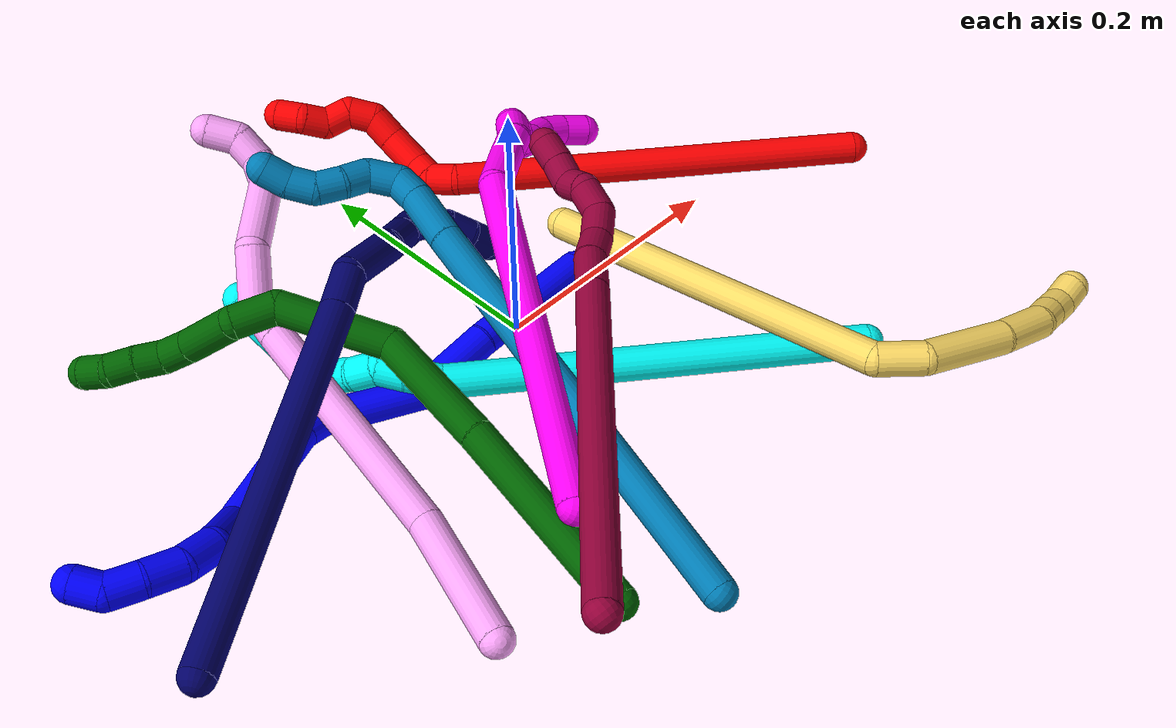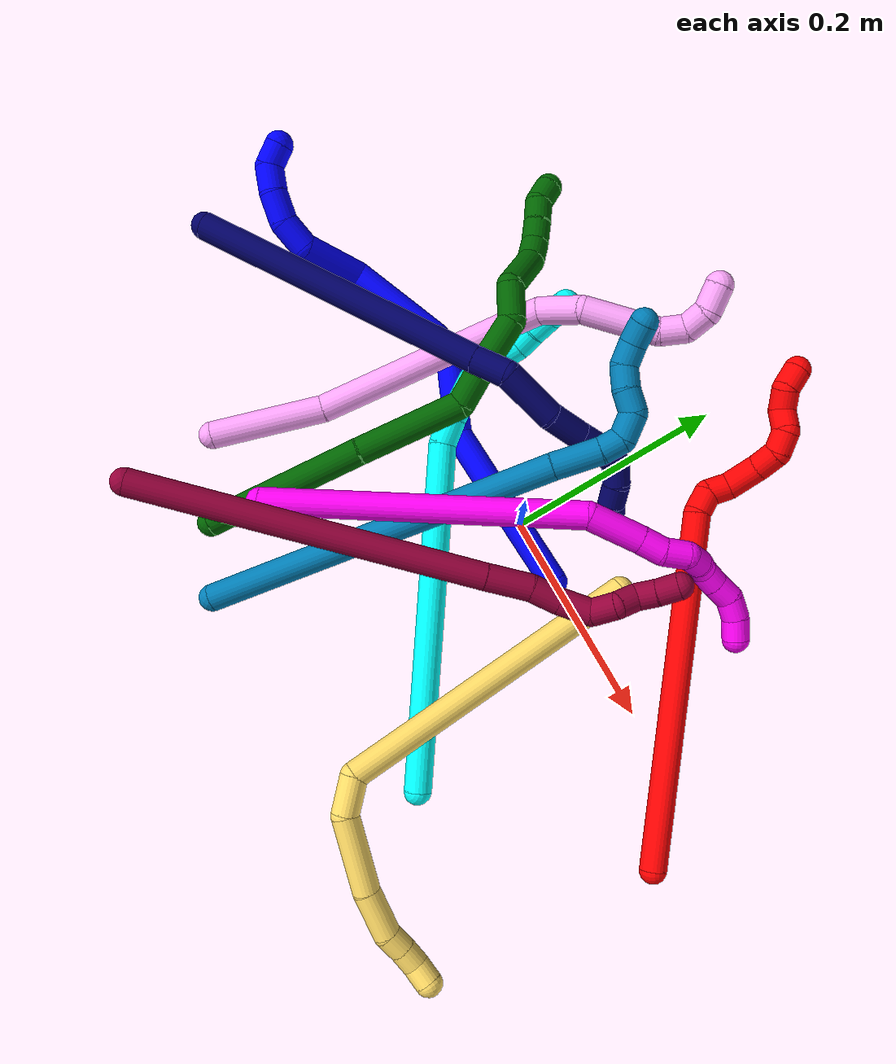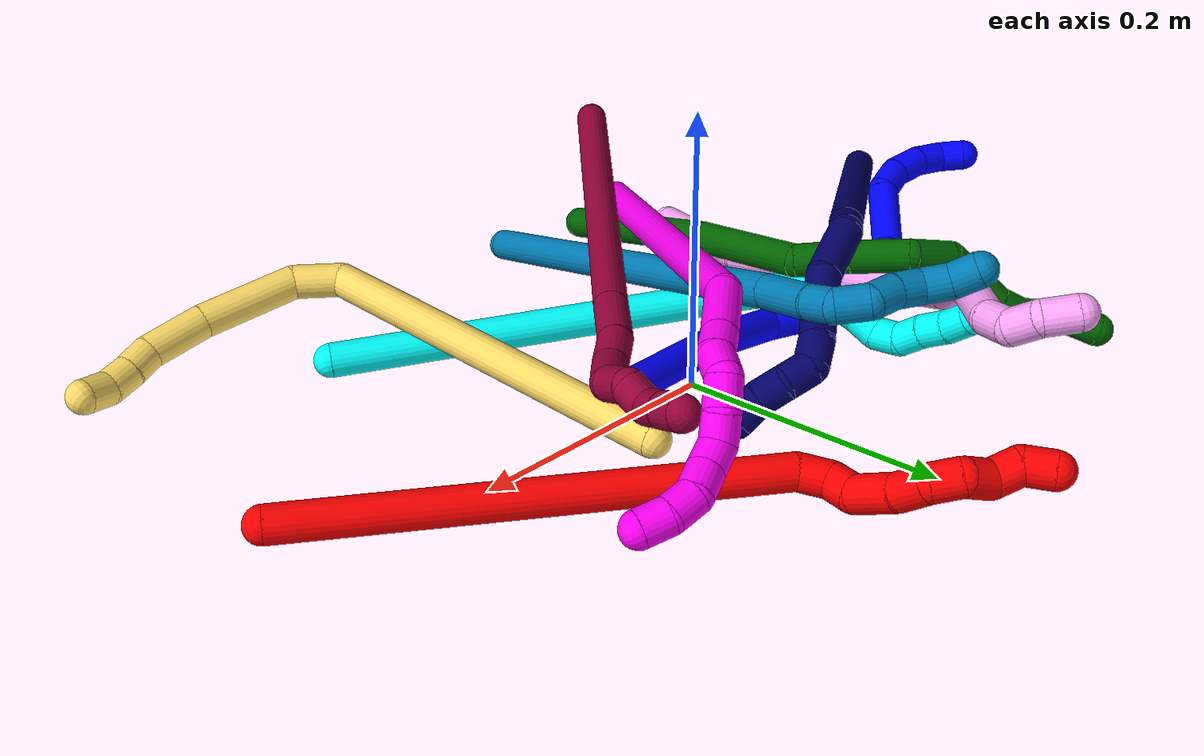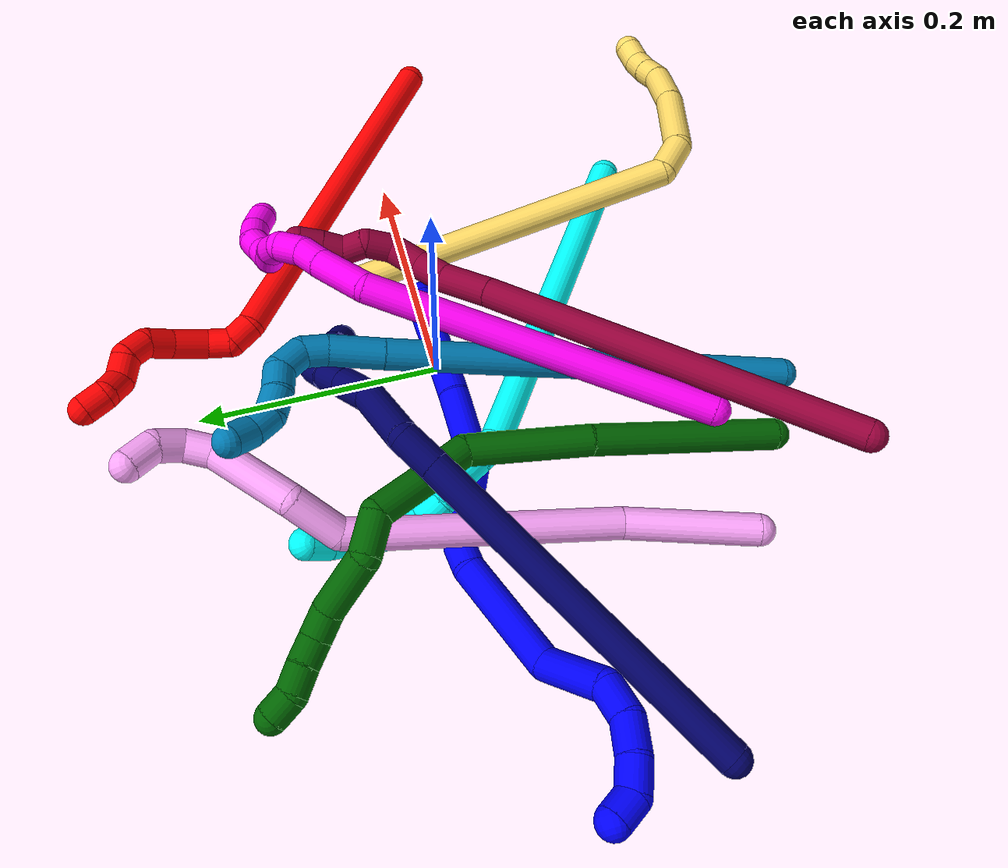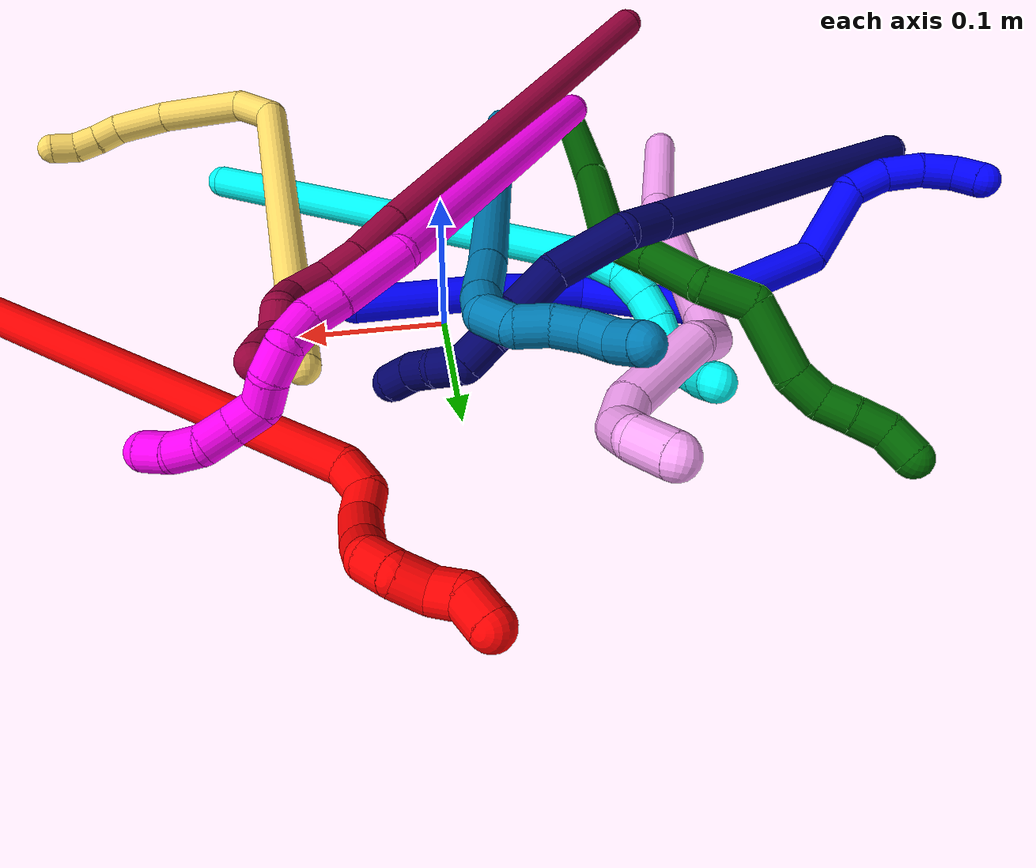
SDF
<sdf version="1.7">
 <world name="default">
  <plugin name="TubeGeneratorPlugin" filename="libtube_generator_plugin.so"/>
  <model name="photoneo_s_sensor">
   <static>1</static>
   <pose>0 0 2 1.57079 1.57079 3.14159</pose>
   <link name="link">
    <inertial><mass>0.1</mass></inertial>
    <sensor name="sensor" type="depth">
     <update_rate>30</update_rate>
     <camera>
      <horizontal_fov>1.22</horizontal_fov>
      <image><width>1920</width><height>1200</height><format>B8G8R8</format></image>
      <clip><near>0.1</near><far>4</far></clip>
      <depth_camera><output>points</output></depth_camera>
     </camera>
     <plugin name="camera_plugin" filename="libgazebo_ros_depth_camera.so">
      <baseline>0.2</baseline>
      <alwaysOn>1</alwaysOn>
      <updateRate>0.0</updateRate>
      <cameraName>camera_ir</cameraName>
      <imageTopicName>/camera/color/image_raw</imageTopicName>
      <cameraInfoTopicName>/camera/color/camera_info</cameraInfoTopicName>
      <depthImageTopicName>/camera/depth/image_raw</depthImageTopicName>
      <depthImageCameraInfoTopicName>/camera/depth/camera_info</depthImageCameraInfoTopicName>
      <pointCloudTopicName>/camera/depth/points</pointCloudTopicName>
      <frameName>fr_optical</frameName>
      <pointCloudCutoff>0.1</pointCloudCutoff>
      <pointCloudCutoffMax>2.0</pointCloudCutoffMax>
      <distortionK1>0</distortionK1>
      <distortionK2>0</distortionK2>
      <distortionK3>0</distortionK3>
      <distortionT1>0</distortionT1>
      <distortionT2>0</distortionT2>
      <CxPrime>0</CxPrime>
      <Cx>0</Cx>
      <Cy>0</Cy>
      <focalLength>0</focalLength>
      <hackBaseline>0</hackBaseline>
     </plugin>
    </sensor>
   </link>
  </model>
  <gravity>0 0 -9.8</gravity>
  <magnetic_field>6e-06 2.3e-05 -4.2e-05</magnetic_field>
  <atmosphere type="adiabatic"/>
  <physics name="default_physics" default="0" type="ode">
   <max_step_size>0.003</max_step_size>
   <real_time_factor>1</real_time_factor>
   <real_time_update_rate>1000</real_time_update_rate>
   <max_contacts>10000</max_contacts>
   <ode>
    <solver>
     <type>quick</type>
     <iters>100</iters>
     <sor>1.3</sor>
     <use_dynamic_moi_rescaling>0</use_dynamic_moi_rescaling>
    </solver>
    <constraints>
     <contact_max_correcting_vel>0</contact_max_correcting_vel>
     <contact_surface_layer>0.001</contact_surface_layer>
     <cfm>0</cfm>
     <erp>0.2</erp>
    </constraints>
   </ode>
  </physics>
  <scene><ambient>0.4 0.4 0.4 1</ambient><background>0.7 0.7 0.7 1</background><shadows>0</shadows></scene>
  <audio><device>default</device></audio>
  <spherical_coordinates>
   <surface_model>EARTH_WGS84</surface_model>
   <latitude_deg>0</latitude_deg>
   <longitude_deg>0</longitude_deg>
   <elevation>0</elevation>
   <heading_deg>0</heading_deg>
  </spherical_coordinates>
  <model name="bin">
   <static>1</static>
   <link name="bottom">
    <collision name="collision-bottom">
     <pose>0 0 -0.01 0 -0 0</pose>
     <geometry><box><size>0.8 0.6 0.02</size></box></geometry>
     <surface>
      <friction><ode><mu>100</mu><mu2>100</mu2></ode></friction>
      <contact><collide_bitmask>65535</collide_bitmask></contact>
     </surface>
    </collision>
   </link>
   <link name="west_wall">
    <collision name="collision-west_wall">
     <pose>-0.41 0 0.1 0 -0 0</pose>
     <geometry><box><size>0.02 0.6 0.2</size></box></geometry>
     <surface>
      <friction><ode><mu>100</mu><mu2>100</mu2></ode></friction>
      <contact><collide_bitmask>65535</collide_bitmask></contact>
     </surface>
    </collision>
   </link>
   <link name="east_wall">
    <collision name="collision-east_wall">
     <pose>0.41 0 0.1 0 -0 0</pose>
     <geometry><box><size>0.02 0.6 0.2</size></box></geometry>
     <surface>
      <friction><ode><mu>100</mu><mu2>100</mu2></ode></friction>
      <contact><collide_bitmask>65535</collide_bitmask></contact>
     </surface>
    </collision>
   </link>
   <link name="south_wall">
    <collision name="collision-south_wall">
     <pose>0 -0.31 0.1 0 -0 0</pose>
     <geometry><box><size>0.8 0.02 0.2</size></box></geometry>
     <surface>
      <friction><ode><mu>100</mu><mu2>100</mu2></ode></friction>
      <contact><collide_bitmask>65535</collide_bitmask></contact>
     </surface>
    </collision>
   </link>
   <link name="north_wall">
    <collision name="collision-north_wall">
     <pose>0 0.31 0.1 0 -0 0</pose>
     <geometry><box><size>0.8 0.02 0.2</size></box></geometry>
     <surface>
      <friction><ode><mu>100</mu><mu2>100</mu2></ode></friction>
      <contact><collide_bitmask>65535</collide_bitmask></contact>
     </surface>
    </collision>
   </link>
  </model>
  <model name="1">
   <static>0</static>
   <link name="1">
    <collision name="collision-cylinder-e_1_1_4">
     <pose>-0.004887 0.000646 0.049521 -0.013041 -0.09836 0.000642</pose>
     <geometry><cylinder><radius>0.0125</radius><length>0.099532</length></cylinder></geometry>
     <surface>
      <friction><ode><mu>1.16</mu><mu2>1.16</mu2><slip1>0</slip1><slip2>0</slip2></ode></friction>
      <contact><ode><kp>1e+06</kp><kd>1</kd><max_vel>0</max_vel><min_depth>0.001</min_depth></ode></contact>
     </surface>
    </collision>
    <visual name="visual-cylinder-e_1_1_4">
     <pose>-0.004887 0.000646 0.049521 -0.013041 -0.09836 0.000642</pose>
     <geometry><cylinder><radius>0.0125</radius><length>0.099532</length></cylinder></geometry>
     <material><ambient>0 0 1 1</ambient></material>
    </visual>
    <collision name="collision-cylinder-e_2_4_5">
     <pose>-0.009027 0.001603 0.129462 -0.010241 0.024556 -0.000126</pose>
     <geometry><cylinder><radius>0.0125</radius><length>0.06086</length></cylinder></geometry>
     <surface>
      <friction><ode><mu>1.16</mu><mu2>1.16</mu2><slip1>0</slip1><slip2>0</slip2></ode></friction>
      <contact><ode><kp>1e+06</kp><kd>1</kd><max_vel>0</max_vel><min_depth>0.001</min_depth></ode></contact>
     </surface>
    </collision>
    <visual name="visual-cylinder-e_2_4_5">
     <pose>-0.009027 0.001603 0.129462 -0.010241 0.024556 -0.000126</pose>
     <geometry><cylinder><radius>0.0125</radius><length>0.06086</length></cylinder></geometry>
     <material><ambient>0 0 1 1</ambient></material>
    </visual>
    <collision name="collision-cylinder-e_3_5_6">
     <pose>-0.011532 -0.01402 0.192831 0.450454 -0.088618 -0.020316</pose>
     <geometry><cylinder><radius>0.0125</radius><length>0.07349</length></cylinder></geometry>
     <surface>
      <friction><ode><mu>1.16</mu><mu2>1.16</mu2><slip1>0</slip1><slip2>0</slip2></ode></friction>
      <contact><ode><kp>1e+06</kp><kd>1</kd><max_vel>0</max_vel><min_depth>0.001</min_depth></ode></contact>
     </surface>
    </collision>
    <visual name="visual-cylinder-e_3_5_6">
     <pose>-0.011532 -0.01402 0.192831 0.450454 -0.088618 -0.020316</pose>
     <geometry><cylinder><radius>0.0125</radius><length>0.07349</length></cylinder></geometry>
     <material><ambient>0 0 1 1</ambient></material>
    </visual>
    <collision name="collision-cylinder-e_4_6_7">
     <pose>-0.017962 -0.029518 0.235701 -0.044067 -0.309741 0.006881</pose>
     <geometry><cylinder><radius>0.0125</radius><length>0.020852</length></cylinder></geometry>
     <surface>
      <friction><ode><mu>1.16</mu><mu2>1.16</mu2><slip1>0</slip1><slip2>0</slip2></ode></friction>
      <contact><ode><kp>1e+06</kp><kd>1</kd><max_vel>0</max_vel><min_depth>0.001</min_depth></ode></contact>
     </surface>
    </collision>
    <visual name="visual-cylinder-e_4_6_7">
     <pose>-0.017962 -0.029518 0.235701 -0.044067 -0.309741 0.006881</pose>
     <geometry><cylinder><radius>0.0125</radius><length>0.020852</length></cylinder></geometry>
     <material><ambient>0 0 1 1</ambient></material>
    </visual>
    <collision name="collision-cylinder-e_5_7_8">
     <pose>-0.029243 -0.014005 0.287217 -0.347709 -0.181143 0.031898</pose>
     <geometry><cylinder><radius>0.0125</radius><length>0.089959</length></cylinder></geometry>
     <surface>
      <friction><ode><mu>1.16</mu><mu2>1.16</mu2><slip1>0</slip1><slip2>0</slip2></ode></friction>
      <contact><ode><kp>1e+06</kp><kd>1</kd><max_vel>0</max_vel><min_depth>0.001</min_depth></ode></contact>
     </surface>
    </collision>
    <visual name="visual-cylinder-e_5_7_8">
     <pose>-0.029243 -0.014005 0.287217 -0.347709 -0.181143 0.031898</pose>
     <geometry><cylinder><radius>0.0125</radius><length>0.089959</length></cylinder></geometry>
     <material><ambient>0 0 1 1</ambient></material>
    </visual>
    <collision name="collision-cylinder-e_6_8_9">
     <pose>-0.058105 0.013491 0.344331 -0.674996 -0.807111 0.29747</pose>
     <geometry><cylinder><radius>0.0125</radius><length>0.057479</length></cylinder></geometry>
     <surface>
      <friction><ode><mu>1.16</mu><mu2>1.16</mu2><slip1>0</slip1><slip2>0</slip2></ode></friction>
      <contact><ode><kp>1e+06</kp><kd>1</kd><max_vel>0</max_vel><min_depth>0.001</min_depth></ode></contact>
     </surface>
    </collision>
    <visual name="visual-cylinder-e_6_8_9">
     <pose>-0.058105 0.013491 0.344331 -0.674996 -0.807111 0.29747</pose>
     <geometry><cylinder><radius>0.0125</radius><length>0.057479</length></cylinder></geometry>
     <material><ambient>0 0 1 1</ambient></material>
    </visual>
    <collision name="collision-cylinder-e_7_9_10">
     <pose>-0.084666 0.027513 0.37218 -0.129082 -0.436574 0.028671</pose>
     <geometry><cylinder><radius>0.0125</radius><length>0.027446</length></cylinder></geometry>
     <surface>
      <friction><ode><mu>1.16</mu><mu2>1.16</mu2><slip1>0</slip1><slip2>0</slip2></ode></friction>
      <contact><ode><kp>1e+06</kp><kd>1</kd><max_vel>0</max_vel><min_depth>0.001</min_depth></ode></contact>
     </surface>
    </collision>
    <visual name="visual-cylinder-e_7_9_10">
     <pose>-0.084666 0.027513 0.37218 -0.129082 -0.436574 0.028671</pose>
     <geometry><cylinder><radius>0.0125</radius><length>0.027446</length></cylinder></geometry>
     <material><ambient>0 0 1 1</ambient></material>
    </visual>
    <collision name="collision-cylinder-e_8_10_11">
     <pose>-0.093983 0.025922 0.396784 0.254423 -0.270437 -0.034798</pose>
     <geometry><cylinder><radius>0.0125</radius><length>0.026314</length></cylinder></geometry>
     <surface>
      <friction><ode><mu>1.16</mu><mu2>1.16</mu2><slip1>0</slip1><slip2>0</slip2></ode></friction>
      <contact><ode><kp>1e+06</kp><kd>1</kd><max_vel>0</max_vel><min_depth>0.001</min_depth></ode></contact>
     </surface>
    </collision>
    <visual name="visual-cylinder-e_8_10_11">
     <pose>-0.093983 0.025922 0.396784 0.254423 -0.270437 -0.034798</pose>
     <geometry><cylinder><radius>0.0125</radius><length>0.026314</length></cylinder></geometry>
     <material><ambient>0 0 1 1</ambient></material>
    </visual>
    <collision name="collision-cylinder-e_9_11_12">
     <pose>-0.098393 0.018154 0.419913 0.398981 -0.07582 -0.015336</pose>
     <geometry><cylinder><radius>0.0125</radius><length>0.023635</length></cylinder></geometry>
     <surface>
      <friction><ode><mu>1.16</mu><mu2>1.16</mu2><slip1>0</slip1><slip2>0</slip2></ode></friction>
      <contact><ode><kp>1e+06</kp><kd>1</kd><max_vel>0</max_vel><min_depth>0.001</min_depth></ode></contact>
     </surface>
    </collision>
    <visual name="visual-cylinder-e_9_11_12">
     <pose>-0.098393 0.018154 0.419913 0.398981 -0.07582 -0.015336</pose>
     <geometry><cylinder><radius>0.0125</radius><length>0.023635</length></cylinder></geometry>
     <material><ambient>0 0 1 1</ambient></material>
    </visual>
    <collision name="collision-cylinder-e_10_12_2">
     <pose>-0.100404 0.00484 0.435948 1.03577 -0.109408 -0.062378</pose>
     <geometry><cylinder><radius>0.0125</radius><length>0.020432</length></cylinder></geometry>
     <surface>
      <friction><ode><mu>1.16</mu><mu2>1.16</mu2><slip1>0</slip1><slip2>0</slip2></ode></friction>
      <contact><ode><kp>1e+06</kp><kd>1</kd><max_vel>0</max_vel><min_depth>0.001</min_depth></ode></contact>
     </surface>
    </collision>
    <visual name="visual-cylinder-e_10_12_2">
     <pose>-0.100404 0.00484 0.435948 1.03577 -0.109408 -0.062378</pose>
     <geometry><cylinder><radius>0.0125</radius><length>0.020432</length></cylinder></geometry>
     <material><ambient>0 0 1 1</ambient></material>
    </visual>
    <collision name="collision-sphere-2">
     <pose>-0.101519 -0.003896 0.441126 0 -0 0</pose>
     <geometry><sphere><radius>0.0125</radius></sphere></geometry>
     <surface>
      <friction><ode><mu>1.16</mu><mu2>1.16</mu2><slip1>0</slip1><slip2>0</slip2></ode></friction>
      <contact><ode><kp>1e+06</kp><kd>1</kd><max_vel>0</max_vel><min_depth>0.001</min_depth></ode></contact>
     </surface>
    </collision>
    <visual name="visual-sphere-2">
     <pose>-0.101519 -0.003896 0.441126 0 -0 0</pose>
     <geometry><sphere><radius>0.0125</radius></sphere></geometry>
     <material><ambient>0 0 1 1</ambient></material>
    </visual>
    <collision name="collision-sphere-12">
     <pose>-0.099288 0.013576 0.43077 0 -0 0</pose>
     <geometry><sphere><radius>0.0125</radius></sphere></geometry>
     <surface>
      <friction><ode><mu>1.16</mu><mu2>1.16</mu2><slip1>0</slip1><slip2>0</slip2></ode></friction>
      <contact><ode><kp>1e+06</kp><kd>1</kd><max_vel>0</max_vel><min_depth>0.001</min_depth></ode></contact>
     </surface>
    </collision>
    <visual name="visual-sphere-12">
     <pose>-0.099288 0.013576 0.43077 0 -0 0</pose>
     <geometry><sphere><radius>0.0125</radius></sphere></geometry>
     <material><ambient>0 0 1 1</ambient></material>
    </visual>
    <collision name="collision-sphere-11">
     <pose>-0.097498 0.022731 0.409055 0 -0 0</pose>
     <geometry><sphere><radius>0.0125</radius></sphere></geometry>
     <surface>
      <friction><ode><mu>1.16</mu><mu2>1.16</mu2><slip1>0</slip1><slip2>0</slip2></ode></friction>
      <contact><ode><kp>1e+06</kp><kd>1</kd><max_vel>0</max_vel><min_depth>0.001</min_depth></ode></contact>
     </surface>
    </collision>
    <visual name="visual-sphere-11">
     <pose>-0.097498 0.022731 0.409055 0 -0 0</pose>
     <geometry><sphere><radius>0.0125</radius></sphere></geometry>
     <material><ambient>0 0 1 1</ambient></material>
    </visual>
    <collision name="collision-sphere-10">
     <pose>-0.090468 0.029113 0.384513 0 -0 0</pose>
     <geometry><sphere><radius>0.0125</radius></sphere></geometry>
     <surface>
      <friction><ode><mu>1.16</mu><mu2>1.16</mu2><slip1>0</slip1><slip2>0</slip2></ode></friction>
      <contact><ode><kp>1e+06</kp><kd>1</kd><max_vel>0</max_vel><min_depth>0.001</min_depth></ode></contact>
     </surface>
    </collision>
    <visual name="visual-sphere-10">
     <pose>-0.090468 0.029113 0.384513 0 -0 0</pose>
     <geometry><sphere><radius>0.0125</radius></sphere></geometry>
     <material><ambient>0 0 1 1</ambient></material>
    </visual>
    <collision name="collision-sphere-9">
     <pose>-0.078863 0.025912 0.359848 0 -0 0</pose>
     <geometry><sphere><radius>0.0125</radius></sphere></geometry>
     <surface>
      <friction><ode><mu>1.16</mu><mu2>1.16</mu2><slip1>0</slip1><slip2>0</slip2></ode></friction>
      <contact><ode><kp>1e+06</kp><kd>1</kd><max_vel>0</max_vel><min_depth>0.001</min_depth></ode></contact>
     </surface>
    </collision>
    <visual name="visual-sphere-9">
     <pose>-0.078863 0.025912 0.359848 0 -0 0</pose>
     <geometry><sphere><radius>0.0125</radius></sphere></geometry>
     <material><ambient>0 0 1 1</ambient></material>
    </visual>
    <collision name="collision-sphere-4">
     <pose>-0.009774 0.001292 0.099042 0 -0 0</pose>
     <geometry><sphere><radius>0.0125</radius></sphere></geometry>
     <surface>
      <friction><ode><mu>1.16</mu><mu2>1.16</mu2><slip1>0</slip1><slip2>0</slip2></ode></friction>
      <contact><ode><kp>1e+06</kp><kd>1</kd><max_vel>0</max_vel><min_depth>0.001</min_depth></ode></contact>
     </surface>
    </collision>
    <visual name="visual-sphere-4">
     <pose>-0.009774 0.001292 0.099042 0 -0 0</pose>
     <geometry><sphere><radius>0.0125</radius></sphere></geometry>
     <material><ambient>0 0 1 1</ambient></material>
    </visual>
    <collision name="collision-sphere-1">
     <geometry><sphere><radius>0.0125</radius></sphere></geometry>
     <surface>
      <friction><ode><mu>1.16</mu><mu2>1.16</mu2><slip1>0</slip1><slip2>0</slip2></ode></friction>
      <contact><ode><kp>1e+06</kp><kd>1</kd><max_vel>0</max_vel><min_depth>0.001</min_depth></ode></contact>
     </surface>
    </collision>
    <visual name="visual-sphere-1">
     <geometry><sphere><radius>0.0125</radius></sphere></geometry>
     <material><ambient>0 0 1 1</ambient></material>
    </visual>
    <collision name="collision-sphere-8">
     <pose>-0.037346 0.001071 0.328813 0 -0 0</pose>
     <geometry><sphere><radius>0.0125</radius></sphere></geometry>
     <surface>
      <friction><ode><mu>1.16</mu><mu2>1.16</mu2><slip1>0</slip1><slip2>0</slip2></ode></friction>
      <contact><ode><kp>1e+06</kp><kd>1</kd><max_vel>0</max_vel><min_depth>0.001</min_depth></ode></contact>
     </surface>
    </collision>
    <visual name="visual-sphere-8">
     <pose>-0.037346 0.001071 0.328813 0 -0 0</pose>
     <geometry><sphere><radius>0.0125</radius></sphere></geometry>
     <material><ambient>0 0 1 1</ambient></material>
    </visual>
    <collision name="collision-sphere-5">
     <pose>-0.00828 0.001915 0.159881 0 -0 0</pose>
     <geometry><sphere><radius>0.0125</radius></sphere></geometry>
     <surface>
      <friction><ode><mu>1.16</mu><mu2>1.16</mu2><slip1>0</slip1><slip2>0</slip2></ode></friction>
      <contact><ode><kp>1e+06</kp><kd>1</kd><max_vel>0</max_vel><min_depth>0.001</min_depth></ode></contact>
     </surface>
    </collision>
    <visual name="visual-sphere-5">
     <pose>-0.00828 0.001915 0.159881 0 -0 0</pose>
     <geometry><sphere><radius>0.0125</radius></sphere></geometry>
     <material><ambient>0 0 1 1</ambient></material>
    </visual>
    <collision name="collision-sphere-6">
     <pose>-0.014784 -0.029955 0.225781 0 -0 0</pose>
     <geometry><sphere><radius>0.0125</radius></sphere></geometry>
     <surface>
      <friction><ode><mu>1.16</mu><mu2>1.16</mu2><slip1>0</slip1><slip2>0</slip2></ode></friction>
      <contact><ode><kp>1e+06</kp><kd>1</kd><max_vel>0</max_vel><min_depth>0.001</min_depth></ode></contact>
     </surface>
    </collision>
    <visual name="visual-sphere-6">
     <pose>-0.014784 -0.029955 0.225781 0 -0 0</pose>
     <geometry><sphere><radius>0.0125</radius></sphere></geometry>
     <material><ambient>0 0 1 1</ambient></material>
    </visual>
    <collision name="collision-sphere-7">
     <pose>-0.02114 -0.029081 0.245621 0 -0 0</pose>
     <geometry><sphere><radius>0.0125</radius></sphere></geometry>
     <surface>
      <friction><ode><mu>1.16</mu><mu2>1.16</mu2><slip1>0</slip1><slip2>0</slip2></ode></friction>
      <contact><ode><kp>1e+06</kp><kd>1</kd><max_vel>0</max_vel><min_depth>0.001</min_depth></ode></contact>
     </surface>
    </collision>
    <visual name="visual-sphere-7">
     <pose>-0.02114 -0.029081 0.245621 0 -0 0</pose>
     <geometry><sphere><radius>0.0125</radius></sphere></geometry>
     <material><ambient>0 0 1 1</ambient></material>
    </visual>
    <inertial>
     <pose>-0.034804 -6e-06 0.234023 0 -0 0</pose>
     <mass>0.5</mass>
     <inertia><ixx>0.000225</ixx><ixy>0</ixy><ixz>0</ixz><iyy>0.00023</iyy><iyz>0</iyz><izz>6e-05</izz></inertia>
    </inertial>
   </link>
   <pose>0.060907 -0.001342 0.022086 -2.37637 1.41749 0.787911</pose>
  </model>
  <model name="2">
   <static>0</static>
   <link name="2">
    <collision name="collision-cylinder-e_1_1_4">
     <pose>-0.124993 0.101107 -0.016683 -1.73433 -0.884073 1.01757</pose>
     <geometry><cylinder><radius>0.0125</radius><length>0.323259</length></cylinder></geometry>
     <surface>
      <friction><ode><mu>1.16</mu><mu2>1.16</mu2><slip1>0</slip1><slip2>0</slip2></ode></friction>
      <contact><ode><kp>1e+06</kp><kd>1</kd><max_vel>0</max_vel><min_depth>0.001</min_depth></ode></contact>
     </surface>
    </collision>
    <visual name="visual-cylinder-e_1_1_4">
     <pose>-0.124993 0.101107 -0.016683 -1.73433 -0.884073 1.01757</pose>
     <geometry><cylinder><radius>0.0125</radius><length>0.323259</length></cylinder></geometry>
     <material><ambient>1 0 0 1</ambient></material>
    </visual>
    <collision name="collision-cylinder-e_2_4_5">
     <pose>-0.255522 0.211422 -0.032246 -1.44967 -0.538138 0.479075</pose>
     <geometry><cylinder><radius>0.0125</radius><length>0.021604</length></cylinder></geometry>
     <surface>
      <friction><ode><mu>1.16</mu><mu2>1.16</mu2><slip1>0</slip1><slip2>0</slip2></ode></friction>
      <contact><ode><kp>1e+06</kp><kd>1</kd><max_vel>0</max_vel><min_depth>0.001</min_depth></ode></contact>
     </surface>
    </collision>
    <visual name="visual-cylinder-e_2_4_5">
     <pose>-0.255522 0.211422 -0.032246 -1.44967 -0.538138 0.479075</pose>
     <geometry><cylinder><radius>0.0125</radius><length>0.021604</length></cylinder></geometry>
     <material><ambient>1 0 0 1</ambient></material>
    </visual>
    <collision name="collision-cylinder-e_3_5_6">
     <pose>-0.261735 0.22796 -0.024152 -0.810419 -0.066781 0.028654</pose>
     <geometry><cylinder><radius>0.0125</radius><length>0.020279</length></cylinder></geometry>
     <surface>
      <friction><ode><mu>1.16</mu><mu2>1.16</mu2><slip1>0</slip1><slip2>0</slip2></ode></friction>
      <contact><ode><kp>1e+06</kp><kd>1</kd><max_vel>0</max_vel><min_depth>0.001</min_depth></ode></contact>
     </surface>
    </collision>
    <visual name="visual-cylinder-e_3_5_6">
     <pose>-0.261735 0.22796 -0.024152 -0.810419 -0.066781 0.028654</pose>
     <geometry><cylinder><radius>0.0125</radius><length>0.020279</length></cylinder></geometry>
     <material><ambient>1 0 0 1</ambient></material>
    </visual>
    <collision name="collision-cylinder-e_4_6_7">
     <pose>-0.270036 0.242819 -0.005516 -0.573183 -0.50225 0.15092</pose>
     <geometry><cylinder><radius>0.0125</radius><length>0.031677</length></cylinder></geometry>
     <surface>
      <friction><ode><mu>1.16</mu><mu2>1.16</mu2><slip1>0</slip1><slip2>0</slip2></ode></friction>
      <contact><ode><kp>1e+06</kp><kd>1</kd><max_vel>0</max_vel><min_depth>0.001</min_depth></ode></contact>
     </surface>
    </collision>
    <visual name="visual-cylinder-e_4_6_7">
     <pose>-0.270036 0.242819 -0.005516 -0.573183 -0.50225 0.15092</pose>
     <geometry><cylinder><radius>0.0125</radius><length>0.031677</length></cylinder></geometry>
     <material><ambient>1 0 0 1</ambient></material>
    </visual>
    <collision name="collision-cylinder-e_5_7_8">
     <pose>-0.284496 0.253969 0.014216 -0.421954 -0.658015 0.145978</pose>
     <geometry><cylinder><radius>0.0125</radius><length>0.022355</length></cylinder></geometry>
     <surface>
      <friction><ode><mu>1.16</mu><mu2>1.16</mu2><slip1>0</slip1><slip2>0</slip2></ode></friction>
      <contact><ode><kp>1e+06</kp><kd>1</kd><max_vel>0</max_vel><min_depth>0.001</min_depth></ode></contact>
     </surface>
    </collision>
    <visual name="visual-cylinder-e_5_7_8">
     <pose>-0.284496 0.253969 0.014216 -0.421954 -0.658015 0.145978</pose>
     <geometry><cylinder><radius>0.0125</radius><length>0.022355</length></cylinder></geometry>
     <material><ambient>1 0 0 1</ambient></material>
    </visual>
    <collision name="collision-cylinder-e_6_8_9">
     <pose>-0.299594 0.263244 0.024358 -1.21913 -0.941013 0.682497</pose>
     <geometry><cylinder><radius>0.0125</radius><length>0.020446</length></cylinder></geometry>
     <surface>
      <friction><ode><mu>1.16</mu><mu2>1.16</mu2><slip1>0</slip1><slip2>0</slip2></ode></friction>
      <contact><ode><kp>1e+06</kp><kd>1</kd><max_vel>0</max_vel><min_depth>0.001</min_depth></ode></contact>
     </surface>
    </collision>
    <visual name="visual-cylinder-e_6_8_9">
     <pose>-0.299594 0.263244 0.024358 -1.21913 -0.941013 0.682497</pose>
     <geometry><cylinder><radius>0.0125</radius><length>0.020446</length></cylinder></geometry>
     <material><ambient>1 0 0 1</ambient></material>
    </visual>
    <collision name="collision-cylinder-e_7_9_10">
     <pose>-0.313996 0.275632 0.0219 -2.163 -0.6476 1.12477</pose>
     <geometry><cylinder><radius>0.0125</radius><length>0.020358</length></cylinder></geometry>
     <surface>
      <friction><ode><mu>1.16</mu><mu2>1.16</mu2><slip1>0</slip1><slip2>0</slip2></ode></friction>
      <contact><ode><kp>1e+06</kp><kd>1</kd><max_vel>0</max_vel><min_depth>0.001</min_depth></ode></contact>
     </surface>
    </collision>
    <visual name="visual-cylinder-e_7_9_10">
     <pose>-0.313996 0.275632 0.0219 -2.163 -0.6476 1.12477</pose>
     <geometry><cylinder><radius>0.0125</radius><length>0.020358</length></cylinder></geometry>
     <material><ambient>1 0 0 1</ambient></material>
    </visual>
    <collision name="collision-cylinder-e_8_10_11">
     <pose>-0.329476 0.285881 0.018151 -1.3519 -1.20289 1.00626</pose>
     <geometry><cylinder><radius>0.0125</radius><length>0.020018</length></cylinder></geometry>
     <surface>
      <friction><ode><mu>1.16</mu><mu2>1.16</mu2><slip1>0</slip1><slip2>0</slip2></ode></friction>
      <contact><ode><kp>1e+06</kp><kd>1</kd><max_vel>0</max_vel><min_depth>0.001</min_depth></ode></contact>
     </surface>
    </collision>
    <visual name="visual-cylinder-e_8_10_11">
     <pose>-0.329476 0.285881 0.018151 -1.3519 -1.20289 1.00626</pose>
     <geometry><cylinder><radius>0.0125</radius><length>0.020018</length></cylinder></geometry>
     <material><ambient>1 0 0 1</ambient></material>
    </visual>
    <collision name="collision-cylinder-e_9_11_2">
     <pose>-0.344443 0.297359 0.021159 -1.29822 -0.597587 0.459201</pose>
     <geometry><cylinder><radius>0.0125</radius><length>0.020004</length></cylinder></geometry>
     <surface>
      <friction><ode><mu>1.16</mu><mu2>1.16</mu2><slip1>0</slip1><slip2>0</slip2></ode></friction>
      <contact><ode><kp>1e+06</kp><kd>1</kd><max_vel>0</max_vel><min_depth>0.001</min_depth></ode></contact>
     </surface>
    </collision>
    <visual name="visual-cylinder-e_9_11_2">
     <pose>-0.344443 0.297359 0.021159 -1.29822 -0.597587 0.459201</pose>
     <geometry><cylinder><radius>0.0125</radius><length>0.020004</length></cylinder></geometry>
     <material><ambient>1 0 0 1</ambient></material>
    </visual>
    <collision name="collision-sphere-2">
     <pose>-0.35007 0.305322 0.023385 0 -0 0</pose>
     <geometry><sphere><radius>0.0125</radius></sphere></geometry>
     <surface>
      <friction><ode><mu>1.16</mu><mu2>1.16</mu2><slip1>0</slip1><slip2>0</slip2></ode></friction>
      <contact><ode><kp>1e+06</kp><kd>1</kd><max_vel>0</max_vel><min_depth>0.001</min_depth></ode></contact>
     </surface>
    </collision>
    <visual name="visual-sphere-2">
     <pose>-0.35007 0.305322 0.023385 0 -0 0</pose>
     <geometry><sphere><radius>0.0125</radius></sphere></geometry>
     <material><ambient>1 0 0 1</ambient></material>
    </visual>
    <collision name="collision-sphere-11">
     <pose>-0.338815 0.289395 0.018933 0 -0 0</pose>
     <geometry><sphere><radius>0.0125</radius></sphere></geometry>
     <surface>
      <friction><ode><mu>1.16</mu><mu2>1.16</mu2><slip1>0</slip1><slip2>0</slip2></ode></friction>
      <contact><ode><kp>1e+06</kp><kd>1</kd><max_vel>0</max_vel><min_depth>0.001</min_depth></ode></contact>
     </surface>
    </collision>
    <visual name="visual-sphere-11">
     <pose>-0.338815 0.289395 0.018933 0 -0 0</pose>
     <geometry><sphere><radius>0.0125</radius></sphere></geometry>
     <material><ambient>1 0 0 1</ambient></material>
    </visual>
    <collision name="collision-sphere-10">
     <pose>-0.320137 0.282367 0.017369 0 -0 0</pose>
     <geometry><sphere><radius>0.0125</radius></sphere></geometry>
     <surface>
      <friction><ode><mu>1.16</mu><mu2>1.16</mu2><slip1>0</slip1><slip2>0</slip2></ode></friction>
      <contact><ode><kp>1e+06</kp><kd>1</kd><max_vel>0</max_vel><min_depth>0.001</min_depth></ode></contact>
     </surface>
    </collision>
    <visual name="visual-sphere-10">
     <pose>-0.320137 0.282367 0.017369 0 -0 0</pose>
     <geometry><sphere><radius>0.0125</radius></sphere></geometry>
     <material><ambient>1 0 0 1</ambient></material>
    </visual>
    <collision name="collision-sphere-9">
     <pose>-0.307856 0.268896 0.026432 0 -0 0</pose>
     <geometry><sphere><radius>0.0125</radius></sphere></geometry>
     <surface>
      <friction><ode><mu>1.16</mu><mu2>1.16</mu2><slip1>0</slip1><slip2>0</slip2></ode></friction>
      <contact><ode><kp>1e+06</kp><kd>1</kd><max_vel>0</max_vel><min_depth>0.001</min_depth></ode></contact>
     </surface>
    </collision>
    <visual name="visual-sphere-9">
     <pose>-0.307856 0.268896 0.026432 0 -0 0</pose>
     <geometry><sphere><radius>0.0125</radius></sphere></geometry>
     <material><ambient>1 0 0 1</ambient></material>
    </visual>
    <collision name="collision-sphere-4">
     <pose>-0.249985 0.202214 -0.033366 0 -0 0</pose>
     <geometry><sphere><radius>0.0125</radius></sphere></geometry>
     <surface>
      <friction><ode><mu>1.16</mu><mu2>1.16</mu2><slip1>0</slip1><slip2>0</slip2></ode></friction>
      <contact><ode><kp>1e+06</kp><kd>1</kd><max_vel>0</max_vel><min_depth>0.001</min_depth></ode></contact>
     </surface>
    </collision>
    <visual name="visual-sphere-4">
     <pose>-0.249985 0.202214 -0.033366 0 -0 0</pose>
     <geometry><sphere><radius>0.0125</radius></sphere></geometry>
     <material><ambient>1 0 0 1</ambient></material>
    </visual>
    <collision name="collision-sphere-1">
     <geometry><sphere><radius>0.0125</radius></sphere></geometry>
     <surface>
      <friction><ode><mu>1.16</mu><mu2>1.16</mu2><slip1>0</slip1><slip2>0</slip2></ode></friction>
      <contact><ode><kp>1e+06</kp><kd>1</kd><max_vel>0</max_vel><min_depth>0.001</min_depth></ode></contact>
     </surface>
    </collision>
    <visual name="visual-sphere-1">
     <geometry><sphere><radius>0.0125</radius></sphere></geometry>
     <material><ambient>1 0 0 1</ambient></material>
    </visual>
    <collision name="collision-sphere-8">
     <pose>-0.291332 0.257591 0.022284 0 -0 0</pose>
     <geometry><sphere><radius>0.0125</radius></sphere></geometry>
     <surface>
      <friction><ode><mu>1.16</mu><mu2>1.16</mu2><slip1>0</slip1><slip2>0</slip2></ode></friction>
      <contact><ode><kp>1e+06</kp><kd>1</kd><max_vel>0</max_vel><min_depth>0.001</min_depth></ode></contact>
     </surface>
    </collision>
    <visual name="visual-sphere-8">
     <pose>-0.291332 0.257591 0.022284 0 -0 0</pose>
     <geometry><sphere><radius>0.0125</radius></sphere></geometry>
     <material><ambient>1 0 0 1</ambient></material>
    </visual>
    <collision name="collision-sphere-5">
     <pose>-0.261058 0.220629 -0.031125 0 -0 0</pose>
     <geometry><sphere><radius>0.0125</radius></sphere></geometry>
     <surface>
      <friction><ode><mu>1.16</mu><mu2>1.16</mu2><slip1>0</slip1><slip2>0</slip2></ode></friction>
      <contact><ode><kp>1e+06</kp><kd>1</kd><max_vel>0</max_vel><min_depth>0.001</min_depth></ode></contact>
     </surface>
    </collision>
    <visual name="visual-sphere-5">
     <pose>-0.261058 0.220629 -0.031125 0 -0 0</pose>
     <geometry><sphere><radius>0.0125</radius></sphere></geometry>
     <material><ambient>1 0 0 1</ambient></material>
    </visual>
    <collision name="collision-sphere-6">
     <pose>-0.262412 0.23529 -0.01718 0 -0 0</pose>
     <geometry><sphere><radius>0.0125</radius></sphere></geometry>
     <surface>
      <friction><ode><mu>1.16</mu><mu2>1.16</mu2><slip1>0</slip1><slip2>0</slip2></ode></friction>
      <contact><ode><kp>1e+06</kp><kd>1</kd><max_vel>0</max_vel><min_depth>0.001</min_depth></ode></contact>
     </surface>
    </collision>
    <visual name="visual-sphere-6">
     <pose>-0.262412 0.23529 -0.01718 0 -0 0</pose>
     <geometry><sphere><radius>0.0125</radius></sphere></geometry>
     <material><ambient>1 0 0 1</ambient></material>
    </visual>
    <collision name="collision-sphere-7">
     <pose>-0.277661 0.250347 0.006148 0 -0 0</pose>
     <geometry><sphere><radius>0.0125</radius></sphere></geometry>
     <surface>
      <friction><ode><mu>1.16</mu><mu2>1.16</mu2><slip1>0</slip1><slip2>0</slip2></ode></friction>
      <contact><ode><kp>1e+06</kp><kd>1</kd><max_vel>0</max_vel><min_depth>0.001</min_depth></ode></contact>
     </surface>
    </collision>
    <visual name="visual-sphere-7">
     <pose>-0.277661 0.250347 0.006148 0 -0 0</pose>
     <geometry><sphere><radius>0.0125</radius></sphere></geometry>
     <material><ambient>1 0 0 1</ambient></material>
    </visual>
    <inertial>
     <pose>-0.184301 0.155816 -0.009412 0 -0 0</pose>
     <mass>0.5</mass>
     <inertia>
      <ixx>0.002454</ixx>
      <ixy>0</ixy>
      <ixz>0</ixz>
      <iyy>0.003157</iyy>
      <iyz>0</iyz>
      <izz>0.000419</izz>
     </inertia>
    </inertial>
   </link>
   <pose>0.328069 -0.056168 0.011117 -0.849916 0.619811 -0.322387</pose>
  </model>
  <model name="3">
   <static>0</static>
   <link name="3">
    <collision name="collision-cylinder-e_1_1_4">
     <pose>-0.129201 0.087422 0.005831 -1.5042 -0.974893 0.920778</pose>
     <geometry><cylinder><radius>0.0125</radius><length>0.312215</length></cylinder></geometry>
     <surface>
      <friction><ode><mu>1.16</mu><mu2>1.16</mu2><slip1>0</slip1><slip2>0</slip2></ode></friction>
      <contact><ode><kp>1e+06</kp><kd>1</kd><max_vel>0</max_vel><min_depth>0.001</min_depth></ode></contact>
     </surface>
    </collision>
    <visual name="visual-cylinder-e_1_1_4">
     <pose>-0.129201 0.087422 0.005831 -1.5042 -0.974893 0.920778</pose>
     <geometry><cylinder><radius>0.0125</radius><length>0.312215</length></cylinder></geometry>
     <material><ambient>0.003922 1 0.996078 1</ambient></material>
    </visual>
    <collision name="collision-cylinder-e_2_4_5">
     <pose>-0.266158 0.184376 0.010337 -1.70889 -0.678335 0.770004</pose>
     <geometry><cylinder><radius>0.0125</radius><length>0.024719</length></cylinder></geometry>
     <surface>
      <friction><ode><mu>1.16</mu><mu2>1.16</mu2><slip1>0</slip1><slip2>0</slip2></ode></friction>
      <contact><ode><kp>1e+06</kp><kd>1</kd><max_vel>0</max_vel><min_depth>0.001</min_depth></ode></contact>
     </surface>
    </collision>
    <visual name="visual-cylinder-e_2_4_5">
     <pose>-0.266158 0.184376 0.010337 -1.70889 -0.678335 0.770004</pose>
     <geometry><cylinder><radius>0.0125</radius><length>0.024719</length></cylinder></geometry>
     <material><ambient>0.003922 1 0.996078 1</ambient></material>
    </visual>
    <collision name="collision-cylinder-e_3_5_6">
     <pose>-0.280143 0.202171 0.00688 -1.82337 -0.630574 0.797011</pose>
     <geometry><cylinder><radius>0.0125</radius><length>0.021133</length></cylinder></geometry>
     <surface>
      <friction><ode><mu>1.16</mu><mu2>1.16</mu2><slip1>0</slip1><slip2>0</slip2></ode></friction>
      <contact><ode><kp>1e+06</kp><kd>1</kd><max_vel>0</max_vel><min_depth>0.001</min_depth></ode></contact>
     </surface>
    </collision>
    <visual name="visual-cylinder-e_3_5_6">
     <pose>-0.280143 0.202171 0.00688 -1.82337 -0.630574 0.797011</pose>
     <geometry><cylinder><radius>0.0125</radius><length>0.021133</length></cylinder></geometry>
     <material><ambient>0.003922 1 0.996078 1</ambient></material>
    </visual>
    <collision name="collision-cylinder-e_4_6_7">
     <pose>-0.294159 0.214182 -0.000633 -2.53317 -0.870972 1.9544</pose>
     <geometry><cylinder><radius>0.0125</radius><length>0.020357</length></cylinder></geometry>
     <surface>
      <friction><ode><mu>1.16</mu><mu2>1.16</mu2><slip1>0</slip1><slip2>0</slip2></ode></friction>
      <contact><ode><kp>1e+06</kp><kd>1</kd><max_vel>0</max_vel><min_depth>0.001</min_depth></ode></contact>
     </surface>
    </collision>
    <visual name="visual-cylinder-e_4_6_7">
     <pose>-0.294159 0.214182 -0.000633 -2.53317 -0.870972 1.9544</pose>
     <geometry><cylinder><radius>0.0125</radius><length>0.020357</length></cylinder></geometry>
     <material><ambient>0.003922 1 0.996078 1</ambient></material>
    </visual>
    <collision name="collision-cylinder-e_5_7_8">
     <pose>-0.308012 0.222329 -0.013096 -2.58577 -0.628968 1.70159</pose>
     <geometry><cylinder><radius>0.0125</radius><length>0.020626</length></cylinder></geometry>
     <surface>
      <friction><ode><mu>1.16</mu><mu2>1.16</mu2><slip1>0</slip1><slip2>0</slip2></ode></friction>
      <contact><ode><kp>1e+06</kp><kd>1</kd><max_vel>0</max_vel><min_depth>0.001</min_depth></ode></contact>
     </surface>
    </collision>
    <visual name="visual-cylinder-e_5_7_8">
     <pose>-0.308012 0.222329 -0.013096 -2.58577 -0.628968 1.70159</pose>
     <geometry><cylinder><radius>0.0125</radius><length>0.020626</length></cylinder></geometry>
     <material><ambient>0.003922 1 0.996078 1</ambient></material>
    </visual>
    <collision name="collision-cylinder-e_6_8_9">
     <pose>-0.318188 0.230783 -0.028394 -2.68311 -0.421604 1.48427</pose>
     <geometry><cylinder><radius>0.0125</radius><length>0.02008</length></cylinder></geometry>
     <surface>
      <friction><ode><mu>1.16</mu><mu2>1.16</mu2><slip1>0</slip1><slip2>0</slip2></ode></friction>
      <contact><ode><kp>1e+06</kp><kd>1</kd><max_vel>0</max_vel><min_depth>0.001</min_depth></ode></contact>
     </surface>
    </collision>
    <visual name="visual-cylinder-e_6_8_9">
     <pose>-0.318188 0.230783 -0.028394 -2.68311 -0.421604 1.48427</pose>
     <geometry><cylinder><radius>0.0125</radius><length>0.02008</length></cylinder></geometry>
     <material><ambient>0.003922 1 0.996078 1</ambient></material>
    </visual>
    <collision name="collision-cylinder-e_7_9_10">
     <pose>-0.323848 0.243355 -0.041839 -2.12151 -0.153937 0.273993</pose>
     <geometry><cylinder><radius>0.0125</radius><length>0.020229</length></cylinder></geometry>
     <surface>
      <friction><ode><mu>1.16</mu><mu2>1.16</mu2><slip1>0</slip1><slip2>0</slip2></ode></friction>
      <contact><ode><kp>1e+06</kp><kd>1</kd><max_vel>0</max_vel><min_depth>0.001</min_depth></ode></contact>
     </surface>
    </collision>
    <visual name="visual-cylinder-e_7_9_10">
     <pose>-0.323848 0.243355 -0.041839 -2.12151 -0.153937 0.273993</pose>
     <geometry><cylinder><radius>0.0125</radius><length>0.020229</length></cylinder></geometry>
     <material><ambient>0.003922 1 0.996078 1</ambient></material>
    </visual>
    <collision name="collision-cylinder-e_8_10_11">
     <pose>-0.326145 0.262014 -0.047368 -1.6002 -0.073508 0.075699</pose>
     <geometry><cylinder><radius>0.0125</radius><length>0.020346</length></cylinder></geometry>
     <surface>
      <friction><ode><mu>1.16</mu><mu2>1.16</mu2><slip1>0</slip1><slip2>0</slip2></ode></friction>
      <contact><ode><kp>1e+06</kp><kd>1</kd><max_vel>0</max_vel><min_depth>0.001</min_depth></ode></contact>
     </surface>
    </collision>
    <visual name="visual-cylinder-e_8_10_11">
     <pose>-0.326145 0.262014 -0.047368 -1.6002 -0.073508 0.075699</pose>
     <geometry><cylinder><radius>0.0125</radius><length>0.020346</length></cylinder></geometry>
     <material><ambient>0.003922 1 0.996078 1</ambient></material>
    </visual>
    <collision name="collision-cylinder-e_9_11_12">
     <pose>-0.328113 0.28205 -0.049388 -1.74308 -0.120883 0.143663</pose>
     <geometry><cylinder><radius>0.0125</radius><length>0.020236</length></cylinder></geometry>
     <surface>
      <friction><ode><mu>1.16</mu><mu2>1.16</mu2><slip1>0</slip1><slip2>0</slip2></ode></friction>
      <contact><ode><kp>1e+06</kp><kd>1</kd><max_vel>0</max_vel><min_depth>0.001</min_depth></ode></contact>
     </surface>
    </collision>
    <visual name="visual-cylinder-e_9_11_12">
     <pose>-0.328113 0.28205 -0.049388 -1.74308 -0.120883 0.143663</pose>
     <geometry><cylinder><radius>0.0125</radius><length>0.020236</length></cylinder></geometry>
     <material><ambient>0.003922 1 0.996078 1</ambient></material>
    </visual>
    <collision name="collision-cylinder-e_10_12_2">
     <pose>-0.329119 0.301967 -0.051474 -1.60708 0.021306 -0.022093</pose>
     <geometry><cylinder><radius>0.0125</radius><length>0.02006</length></cylinder></geometry>
     <surface>
      <friction><ode><mu>1.16</mu><mu2>1.16</mu2><slip1>0</slip1><slip2>0</slip2></ode></friction>
      <contact><ode><kp>1e+06</kp><kd>1</kd><max_vel>0</max_vel><min_depth>0.001</min_depth></ode></contact>
     </surface>
    </collision>
    <visual name="visual-cylinder-e_10_12_2">
     <pose>-0.329119 0.301967 -0.051474 -1.60708 0.021306 -0.022093</pose>
     <geometry><cylinder><radius>0.0125</radius><length>0.02006</length></cylinder></geometry>
     <material><ambient>0.003922 1 0.996078 1</ambient></material>
    </visual>
    <collision name="collision-sphere-2">
     <pose>-0.328906 0.311988 -0.051838 0 -0 0</pose>
     <geometry><sphere><radius>0.0125</radius></sphere></geometry>
     <surface>
      <friction><ode><mu>1.16</mu><mu2>1.16</mu2><slip1>0</slip1><slip2>0</slip2></ode></friction>
      <contact><ode><kp>1e+06</kp><kd>1</kd><max_vel>0</max_vel><min_depth>0.001</min_depth></ode></contact>
     </surface>
    </collision>
    <visual name="visual-sphere-2">
     <pose>-0.328906 0.311988 -0.051838 0 -0 0</pose>
     <geometry><sphere><radius>0.0125</radius></sphere></geometry>
     <material><ambient>0.003922 1 0.996078 1</ambient></material>
    </visual>
    <collision name="collision-sphere-12">
     <pose>-0.329333 0.291946 -0.05111 0 -0 0</pose>
     <geometry><sphere><radius>0.0125</radius></sphere></geometry>
     <surface>
      <friction><ode><mu>1.16</mu><mu2>1.16</mu2><slip1>0</slip1><slip2>0</slip2></ode></friction>
      <contact><ode><kp>1e+06</kp><kd>1</kd><max_vel>0</max_vel><min_depth>0.001</min_depth></ode></contact>
     </surface>
    </collision>
    <visual name="visual-sphere-12">
     <pose>-0.329333 0.291946 -0.05111 0 -0 0</pose>
     <geometry><sphere><radius>0.0125</radius></sphere></geometry>
     <material><ambient>0.003922 1 0.996078 1</ambient></material>
    </visual>
    <collision name="collision-sphere-11">
     <pose>-0.326893 0.272155 -0.047666 0 -0 0</pose>
     <geometry><sphere><radius>0.0125</radius></sphere></geometry>
     <surface>
      <friction><ode><mu>1.16</mu><mu2>1.16</mu2><slip1>0</slip1><slip2>0</slip2></ode></friction>
      <contact><ode><kp>1e+06</kp><kd>1</kd><max_vel>0</max_vel><min_depth>0.001</min_depth></ode></contact>
     </surface>
    </collision>
    <visual name="visual-sphere-11">
     <pose>-0.326893 0.272155 -0.047666 0 -0 0</pose>
     <geometry><sphere><radius>0.0125</radius></sphere></geometry>
     <material><ambient>0.003922 1 0.996078 1</ambient></material>
    </visual>
    <collision name="collision-sphere-10">
     <pose>-0.325398 0.251873 -0.04707 0 -0 0</pose>
     <geometry><sphere><radius>0.0125</radius></sphere></geometry>
     <surface>
      <friction><ode><mu>1.16</mu><mu2>1.16</mu2><slip1>0</slip1><slip2>0</slip2></ode></friction>
      <contact><ode><kp>1e+06</kp><kd>1</kd><max_vel>0</max_vel><min_depth>0.001</min_depth></ode></contact>
     </surface>
    </collision>
    <visual name="visual-sphere-10">
     <pose>-0.325398 0.251873 -0.04707 0 -0 0</pose>
     <geometry><sphere><radius>0.0125</radius></sphere></geometry>
     <material><ambient>0.003922 1 0.996078 1</ambient></material>
    </visual>
    <collision name="collision-sphere-9">
     <pose>-0.322297 0.234838 -0.036609 0 -0 0</pose>
     <geometry><sphere><radius>0.0125</radius></sphere></geometry>
     <surface>
      <friction><ode><mu>1.16</mu><mu2>1.16</mu2><slip1>0</slip1><slip2>0</slip2></ode></friction>
      <contact><ode><kp>1e+06</kp><kd>1</kd><max_vel>0</max_vel><min_depth>0.001</min_depth></ode></contact>
     </surface>
    </collision>
    <visual name="visual-sphere-9">
     <pose>-0.322297 0.234838 -0.036609 0 -0 0</pose>
     <geometry><sphere><radius>0.0125</radius></sphere></geometry>
     <material><ambient>0.003922 1 0.996078 1</ambient></material>
    </visual>
    <collision name="collision-sphere-4">
     <pose>-0.258402 0.174844 0.011662 0 -0 0</pose>
     <geometry><sphere><radius>0.0125</radius></sphere></geometry>
     <surface>
      <friction><ode><mu>1.16</mu><mu2>1.16</mu2><slip1>0</slip1><slip2>0</slip2></ode></friction>
      <contact><ode><kp>1e+06</kp><kd>1</kd><max_vel>0</max_vel><min_depth>0.001</min_depth></ode></contact>
     </surface>
    </collision>
    <visual name="visual-sphere-4">
     <pose>-0.258402 0.174844 0.011662 0 -0 0</pose>
     <geometry><sphere><radius>0.0125</radius></sphere></geometry>
     <material><ambient>0.003922 1 0.996078 1</ambient></material>
    </visual>
    <collision name="collision-sphere-1">
     <geometry><sphere><radius>0.0125</radius></sphere></geometry>
     <surface>
      <friction><ode><mu>1.16</mu><mu2>1.16</mu2><slip1>0</slip1><slip2>0</slip2></ode></friction>
      <contact><ode><kp>1e+06</kp><kd>1</kd><max_vel>0</max_vel><min_depth>0.001</min_depth></ode></contact>
     </surface>
    </collision>
    <visual name="visual-sphere-1">
     <geometry><sphere><radius>0.0125</radius></sphere></geometry>
     <material><ambient>0.003922 1 0.996078 1</ambient></material>
    </visual>
    <collision name="collision-sphere-8">
     <pose>-0.31408 0.226729 -0.02018 0 -0 0</pose>
     <geometry><sphere><radius>0.0125</radius></sphere></geometry>
     <surface>
      <friction><ode><mu>1.16</mu><mu2>1.16</mu2><slip1>0</slip1><slip2>0</slip2></ode></friction>
      <contact><ode><kp>1e+06</kp><kd>1</kd><max_vel>0</max_vel><min_depth>0.001</min_depth></ode></contact>
     </surface>
    </collision>
    <visual name="visual-sphere-8">
     <pose>-0.31408 0.226729 -0.02018 0 -0 0</pose>
     <geometry><sphere><radius>0.0125</radius></sphere></geometry>
     <material><ambient>0.003922 1 0.996078 1</ambient></material>
    </visual>
    <collision name="collision-sphere-5">
     <pose>-0.273913 0.193907 0.009012 0 -0 0</pose>
     <geometry><sphere><radius>0.0125</radius></sphere></geometry>
     <surface>
      <friction><ode><mu>1.16</mu><mu2>1.16</mu2><slip1>0</slip1><slip2>0</slip2></ode></friction>
      <contact><ode><kp>1e+06</kp><kd>1</kd><max_vel>0</max_vel><min_depth>0.001</min_depth></ode></contact>
     </surface>
    </collision>
    <visual name="visual-sphere-5">
     <pose>-0.273913 0.193907 0.009012 0 -0 0</pose>
     <geometry><sphere><radius>0.0125</radius></sphere></geometry>
     <material><ambient>0.003922 1 0.996078 1</ambient></material>
    </visual>
    <collision name="collision-sphere-6">
     <pose>-0.286373 0.210434 0.004747 0 -0 0</pose>
     <geometry><sphere><radius>0.0125</radius></sphere></geometry>
     <surface>
      <friction><ode><mu>1.16</mu><mu2>1.16</mu2><slip1>0</slip1><slip2>0</slip2></ode></friction>
      <contact><ode><kp>1e+06</kp><kd>1</kd><max_vel>0</max_vel><min_depth>0.001</min_depth></ode></contact>
     </surface>
    </collision>
    <visual name="visual-sphere-6">
     <pose>-0.286373 0.210434 0.004747 0 -0 0</pose>
     <geometry><sphere><radius>0.0125</radius></sphere></geometry>
     <material><ambient>0.003922 1 0.996078 1</ambient></material>
    </visual>
    <collision name="collision-sphere-7">
     <pose>-0.301945 0.217929 -0.006012 0 -0 0</pose>
     <geometry><sphere><radius>0.0125</radius></sphere></geometry>
     <surface>
      <friction><ode><mu>1.16</mu><mu2>1.16</mu2><slip1>0</slip1><slip2>0</slip2></ode></friction>
      <contact><ode><kp>1e+06</kp><kd>1</kd><max_vel>0</max_vel><min_depth>0.001</min_depth></ode></contact>
     </surface>
    </collision>
    <visual name="visual-sphere-7">
     <pose>-0.301945 0.217929 -0.006012 0 -0 0</pose>
     <geometry><sphere><radius>0.0125</radius></sphere></geometry>
     <material><ambient>0.003922 1 0.996078 1</ambient></material>
    </visual>
    <inertial>
     <pose>-0.195994 0.143446 -0.004948 0 -0 0</pose>
     <mass>0.5</mass>
     <inertia>
      <ixx>0.001992</ixx>
      <ixy>0</ixy>
      <ixz>0</ixz>
      <iyy>0.002949</iyy>
      <iyz>0</iyz>
      <izz>0.000673</izz>
     </inertia>
    </inertial>
   </link>
   <pose>0.160418 -0.201795 0.012488 0.67107 -0.35213 -0.176699</pose>
  </model>
  <model name="4">
   <static>0</static>
   <link name="4">
    <collision name="collision-cylinder-e_1_1_4">
     <pose>0.007667 0.036518 -0.036191 -2.3517 0.148024 -0.352071</pose>
     <geometry><cylinder><radius>0.0125</radius><length>0.103964</length></cylinder></geometry>
     <surface>
      <friction><ode><mu>1.16</mu><mu2>1.16</mu2><slip1>0</slip1><slip2>0</slip2></ode></friction>
      <contact><ode><kp>1e+06</kp><kd>1</kd><max_vel>0</max_vel><min_depth>0.001</min_depth></ode></contact>
     </surface>
    </collision>
    <visual name="visual-cylinder-e_1_1_4">
     <pose>0.007667 0.036518 -0.036191 -2.3517 0.148024 -0.352071</pose>
     <geometry><cylinder><radius>0.0125</radius><length>0.103964</length></cylinder></geometry>
     <material><ambient>1 0.65098 0.996078 1</ambient></material>
    </visual>
    <collision name="collision-cylinder-e_2_4_5">
     <pose>0.017934 0.149115 -0.124716 -2.17335 0.028155 -0.053531</pose>
     <geometry><cylinder><radius>0.0125</radius><length>0.184755</length></cylinder></geometry>
     <surface>
      <friction><ode><mu>1.16</mu><mu2>1.16</mu2><slip1>0</slip1><slip2>0</slip2></ode></friction>
      <contact><ode><kp>1e+06</kp><kd>1</kd><max_vel>0</max_vel><min_depth>0.001</min_depth></ode></contact>
     </surface>
    </collision>
    <visual name="visual-cylinder-e_2_4_5">
     <pose>0.017934 0.149115 -0.124716 -2.17335 0.028155 -0.053531</pose>
     <geometry><cylinder><radius>0.0125</radius><length>0.184755</length></cylinder></geometry>
     <material><ambient>1 0.65098 0.996078 1</ambient></material>
    </visual>
    <collision name="collision-cylinder-e_3_5_6">
     <pose>0.02152 0.237388 -0.184864 -2.14068 0.067945 -0.124125</pose>
     <geometry><cylinder><radius>0.0125</radius><length>0.029032</length></cylinder></geometry>
     <surface>
      <friction><ode><mu>1.16</mu><mu2>1.16</mu2><slip1>0</slip1><slip2>0</slip2></ode></friction>
      <contact><ode><kp>1e+06</kp><kd>1</kd><max_vel>0</max_vel><min_depth>0.001</min_depth></ode></contact>
     </surface>
    </collision>
    <visual name="visual-cylinder-e_3_5_6">
     <pose>0.02152 0.237388 -0.184864 -2.14068 0.067945 -0.124125</pose>
     <geometry><cylinder><radius>0.0125</radius><length>0.029032</length></cylinder></geometry>
     <material><ambient>1 0.65098 0.996078 1</ambient></material>
    </visual>
    <collision name="collision-cylinder-e_4_6_7">
     <pose>0.034564 0.267191 -0.197238 -1.82422 0.585386 -0.742564</pose>
     <geometry><cylinder><radius>0.0125</radius><length>0.04365</length></cylinder></geometry>
     <surface>
      <friction><ode><mu>1.16</mu><mu2>1.16</mu2><slip1>0</slip1><slip2>0</slip2></ode></friction>
      <contact><ode><kp>1e+06</kp><kd>1</kd><max_vel>0</max_vel><min_depth>0.001</min_depth></ode></contact>
     </surface>
    </collision>
    <visual name="visual-cylinder-e_4_6_7">
     <pose>0.034564 0.267191 -0.197238 -1.82422 0.585386 -0.742564</pose>
     <geometry><cylinder><radius>0.0125</radius><length>0.04365</length></cylinder></geometry>
     <material><ambient>1 0.65098 0.996078 1</ambient></material>
    </visual>
    <collision name="collision-cylinder-e_5_7_8">
     <pose>0.067538 0.300994 -0.223325 -2.49664 0.660234 -1.59596</pose>
     <geometry><cylinder><radius>0.0125</radius><length>0.068206</length></cylinder></geometry>
     <surface>
      <friction><ode><mu>1.16</mu><mu2>1.16</mu2><slip1>0</slip1><slip2>0</slip2></ode></friction>
      <contact><ode><kp>1e+06</kp><kd>1</kd><max_vel>0</max_vel><min_depth>0.001</min_depth></ode></contact>
     </surface>
    </collision>
    <visual name="visual-cylinder-e_5_7_8">
     <pose>0.067538 0.300994 -0.223325 -2.49664 0.660234 -1.59596</pose>
     <geometry><cylinder><radius>0.0125</radius><length>0.068206</length></cylinder></geometry>
     <material><ambient>1 0.65098 0.996078 1</ambient></material>
    </visual>
    <collision name="collision-cylinder-e_6_8_9">
     <pose>0.092059 0.32567 -0.252383 -2.297 0.307763 -0.664782</pose>
     <geometry><cylinder><radius>0.0125</radius><length>0.023808</length></cylinder></geometry>
     <surface>
      <friction><ode><mu>1.16</mu><mu2>1.16</mu2><slip1>0</slip1><slip2>0</slip2></ode></friction>
      <contact><ode><kp>1e+06</kp><kd>1</kd><max_vel>0</max_vel><min_depth>0.001</min_depth></ode></contact>
     </surface>
    </collision>
    <visual name="visual-cylinder-e_6_8_9">
     <pose>0.092059 0.32567 -0.252383 -2.297 0.307763 -0.664782</pose>
     <geometry><cylinder><radius>0.0125</radius><length>0.023808</length></cylinder></geometry>
     <material><ambient>1 0.65098 0.996078 1</ambient></material>
    </visual>
    <collision name="collision-cylinder-e_7_9_10">
     <pose>0.094918 0.345248 -0.261937 -1.75091 -0.06618 0.079306</pose>
     <geometry><cylinder><radius>0.0125</radius><length>0.022607</length></cylinder></geometry>
     <surface>
      <friction><ode><mu>1.16</mu><mu2>1.16</mu2><slip1>0</slip1><slip2>0</slip2></ode></friction>
      <contact><ode><kp>1e+06</kp><kd>1</kd><max_vel>0</max_vel><min_depth>0.001</min_depth></ode></contact>
     </surface>
    </collision>
    <visual name="visual-cylinder-e_7_9_10">
     <pose>0.094918 0.345248 -0.261937 -1.75091 -0.06618 0.079306</pose>
     <geometry><cylinder><radius>0.0125</radius><length>0.022607</length></cylinder></geometry>
     <material><ambient>1 0.65098 0.996078 1</ambient></material>
    </visual>
    <collision name="collision-cylinder-e_8_10_2">
     <pose>0.086924 0.365568 -0.266437 -1.83333 -0.649074 0.82697</pose>
     <geometry><cylinder><radius>0.0125</radius><length>0.023978</length></cylinder></geometry>
     <surface>
      <friction><ode><mu>1.16</mu><mu2>1.16</mu2><slip1>0</slip1><slip2>0</slip2></ode></friction>
      <contact><ode><kp>1e+06</kp><kd>1</kd><max_vel>0</max_vel><min_depth>0.001</min_depth></ode></contact>
     </surface>
    </collision>
    <visual name="visual-cylinder-e_8_10_2">
     <pose>0.086924 0.365568 -0.266437 -1.83333 -0.649074 0.82697</pose>
     <geometry><cylinder><radius>0.0125</radius><length>0.023978</length></cylinder></geometry>
     <material><ambient>1 0.65098 0.996078 1</ambient></material>
    </visual>
    <collision name="collision-sphere-2">
     <pose>0.079677 0.374792 -0.268915 0 -0 0</pose>
     <geometry><sphere><radius>0.0125</radius></sphere></geometry>
     <surface>
      <friction><ode><mu>1.16</mu><mu2>1.16</mu2><slip1>0</slip1><slip2>0</slip2></ode></friction>
      <contact><ode><kp>1e+06</kp><kd>1</kd><max_vel>0</max_vel><min_depth>0.001</min_depth></ode></contact>
     </surface>
    </collision>
    <visual name="visual-sphere-2">
     <pose>0.079677 0.374792 -0.268915 0 -0 0</pose>
     <geometry><sphere><radius>0.0125</radius></sphere></geometry>
     <material><ambient>1 0.65098 0.996078 1</ambient></material>
    </visual>
    <collision name="collision-sphere-10">
     <pose>0.09417 0.356345 -0.263958 0 -0 0</pose>
     <geometry><sphere><radius>0.0125</radius></sphere></geometry>
     <surface>
      <friction><ode><mu>1.16</mu><mu2>1.16</mu2><slip1>0</slip1><slip2>0</slip2></ode></friction>
      <contact><ode><kp>1e+06</kp><kd>1</kd><max_vel>0</max_vel><min_depth>0.001</min_depth></ode></contact>
     </surface>
    </collision>
    <visual name="visual-sphere-10">
     <pose>0.09417 0.356345 -0.263958 0 -0 0</pose>
     <geometry><sphere><radius>0.0125</radius></sphere></geometry>
     <material><ambient>1 0.65098 0.996078 1</ambient></material>
    </visual>
    <collision name="collision-sphere-9">
     <pose>0.095665 0.334152 -0.259917 0 -0 0</pose>
     <geometry><sphere><radius>0.0125</radius></sphere></geometry>
     <surface>
      <friction><ode><mu>1.16</mu><mu2>1.16</mu2><slip1>0</slip1><slip2>0</slip2></ode></friction>
      <contact><ode><kp>1e+06</kp><kd>1</kd><max_vel>0</max_vel><min_depth>0.001</min_depth></ode></contact>
     </surface>
    </collision>
    <visual name="visual-sphere-9">
     <pose>0.095665 0.334152 -0.259917 0 -0 0</pose>
     <geometry><sphere><radius>0.0125</radius></sphere></geometry>
     <material><ambient>1 0.65098 0.996078 1</ambient></material>
    </visual>
    <collision name="collision-sphere-4">
     <pose>0.015333 0.073036 -0.072383 0 -0 0</pose>
     <geometry><sphere><radius>0.0125</radius></sphere></geometry>
     <surface>
      <friction><ode><mu>1.16</mu><mu2>1.16</mu2><slip1>0</slip1><slip2>0</slip2></ode></friction>
      <contact><ode><kp>1e+06</kp><kd>1</kd><max_vel>0</max_vel><min_depth>0.001</min_depth></ode></contact>
     </surface>
    </collision>
    <visual name="visual-sphere-4">
     <pose>0.015333 0.073036 -0.072383 0 -0 0</pose>
     <geometry><sphere><radius>0.0125</radius></sphere></geometry>
     <material><ambient>1 0.65098 0.996078 1</ambient></material>
    </visual>
    <collision name="collision-sphere-1">
     <geometry><sphere><radius>0.0125</radius></sphere></geometry>
     <surface>
      <friction><ode><mu>1.16</mu><mu2>1.16</mu2><slip1>0</slip1><slip2>0</slip2></ode></friction>
      <contact><ode><kp>1e+06</kp><kd>1</kd><max_vel>0</max_vel><min_depth>0.001</min_depth></ode></contact>
     </surface>
    </collision>
    <visual name="visual-sphere-1">
     <geometry><sphere><radius>0.0125</radius></sphere></geometry>
     <material><ambient>1 0.65098 0.996078 1</ambient></material>
    </visual>
    <collision name="collision-sphere-8">
     <pose>0.088453 0.317187 -0.24485 0 -0 0</pose>
     <geometry><sphere><radius>0.0125</radius></sphere></geometry>
     <surface>
      <friction><ode><mu>1.16</mu><mu2>1.16</mu2><slip1>0</slip1><slip2>0</slip2></ode></friction>
      <contact><ode><kp>1e+06</kp><kd>1</kd><max_vel>0</max_vel><min_depth>0.001</min_depth></ode></contact>
     </surface>
    </collision>
    <visual name="visual-sphere-8">
     <pose>0.088453 0.317187 -0.24485 0 -0 0</pose>
     <geometry><sphere><radius>0.0125</radius></sphere></geometry>
     <material><ambient>1 0.65098 0.996078 1</ambient></material>
    </visual>
    <collision name="collision-sphere-5">
     <pose>0.020534 0.225194 -0.17705 0 -0 0</pose>
     <geometry><sphere><radius>0.0125</radius></sphere></geometry>
     <surface>
      <friction><ode><mu>1.16</mu><mu2>1.16</mu2><slip1>0</slip1><slip2>0</slip2></ode></friction>
      <contact><ode><kp>1e+06</kp><kd>1</kd><max_vel>0</max_vel><min_depth>0.001</min_depth></ode></contact>
     </surface>
    </collision>
    <visual name="visual-sphere-5">
     <pose>0.020534 0.225194 -0.17705 0 -0 0</pose>
     <geometry><sphere><radius>0.0125</radius></sphere></geometry>
     <material><ambient>1 0.65098 0.996078 1</ambient></material>
    </visual>
    <collision name="collision-sphere-6">
     <pose>0.022505 0.249581 -0.192678 0 -0 0</pose>
     <geometry><sphere><radius>0.0125</radius></sphere></geometry>
     <surface>
      <friction><ode><mu>1.16</mu><mu2>1.16</mu2><slip1>0</slip1><slip2>0</slip2></ode></friction>
      <contact><ode><kp>1e+06</kp><kd>1</kd><max_vel>0</max_vel><min_depth>0.001</min_depth></ode></contact>
     </surface>
    </collision>
    <visual name="visual-sphere-6">
     <pose>0.022505 0.249581 -0.192678 0 -0 0</pose>
     <geometry><sphere><radius>0.0125</radius></sphere></geometry>
     <material><ambient>1 0.65098 0.996078 1</ambient></material>
    </visual>
    <collision name="collision-sphere-7">
     <pose>0.046623 0.284801 -0.201799 0 -0 0</pose>
     <geometry><sphere><radius>0.0125</radius></sphere></geometry>
     <surface>
      <friction><ode><mu>1.16</mu><mu2>1.16</mu2><slip1>0</slip1><slip2>0</slip2></ode></friction>
      <contact><ode><kp>1e+06</kp><kd>1</kd><max_vel>0</max_vel><min_depth>0.001</min_depth></ode></contact>
     </surface>
    </collision>
    <visual name="visual-sphere-7">
     <pose>0.046623 0.284801 -0.201799 0 -0 0</pose>
     <geometry><sphere><radius>0.0125</radius></sphere></geometry>
     <material><ambient>1 0.65098 0.996078 1</ambient></material>
    </visual>
    <inertial>
     <pose>0.034544 0.189509 -0.148664 0 -0 0</pose>
     <mass>0.5</mass>
     <inertia>
      <ixx>0.000551</ixx>
      <ixy>0</ixy>
      <ixz>0</ixz>
      <iyy>-0.000412</iyy>
      <iyz>0</iyz>
      <izz>-0.000608</izz>
     </inertia>
    </inertial>
   </link>
   <pose>-0.21147 -0.19928 0.017238 0.760988 -0.270265 -0.153567</pose>
  </model>
  <model name="5">
   <static>0</static>
   <link name="5">
    <collision name="collision-cylinder-e_1_1_4">
     <pose>-0.01083 -0.043863 0.136787 0.310309 -0.07525 -0.011775</pose>
     <geometry><cylinder><radius>0.0125</radius><length>0.288111</length></cylinder></geometry>
     <surface>
      <friction><ode><mu>1.16</mu><mu2>1.16</mu2><slip1>0</slip1><slip2>0</slip2></ode></friction>
      <contact><ode><kp>1e+06</kp><kd>1</kd><max_vel>0</max_vel><min_depth>0.001</min_depth></ode></contact>
     </surface>
    </collision>
    <visual name="visual-cylinder-e_1_1_4">
     <pose>-0.01083 -0.043863 0.136787 0.310309 -0.07525 -0.011775</pose>
     <geometry><cylinder><radius>0.0125</radius><length>0.288111</length></cylinder></geometry>
     <material><ambient>1 0.858824 0.4 1</ambient></material>
    </visual>
    <collision name="collision-cylinder-e_2_4_5">
     <pose>-0.011014 -0.095072 0.285598 0.548375 0.647049 0.188068</pose>
     <geometry><cylinder><radius>0.0125</radius><length>0.03532</length></cylinder></geometry>
     <surface>
      <friction><ode><mu>1.16</mu><mu2>1.16</mu2><slip1>0</slip1><slip2>0</slip2></ode></friction>
      <contact><ode><kp>1e+06</kp><kd>1</kd><max_vel>0</max_vel><min_depth>0.001</min_depth></ode></contact>
     </surface>
    </collision>
    <visual name="visual-cylinder-e_2_4_5">
     <pose>-0.011014 -0.095072 0.285598 0.548375 0.647049 0.188068</pose>
     <geometry><cylinder><radius>0.0125</radius><length>0.03532</length></cylinder></geometry>
     <material><ambient>1 0.858824 0.4 1</ambient></material>
    </visual>
    <collision name="collision-cylinder-e_3_5_6">
     <pose>0.030505 -0.118653 0.306422 1.07413 1.03172 0.651281</pose>
     <geometry><cylinder><radius>0.0125</radius><length>0.07195</length></cylinder></geometry>
     <surface>
      <friction><ode><mu>1.16</mu><mu2>1.16</mu2><slip1>0</slip1><slip2>0</slip2></ode></friction>
      <contact><ode><kp>1e+06</kp><kd>1</kd><max_vel>0</max_vel><min_depth>0.001</min_depth></ode></contact>
     </surface>
    </collision>
    <visual name="visual-cylinder-e_3_5_6">
     <pose>0.030505 -0.118653 0.306422 1.07413 1.03172 0.651281</pose>
     <geometry><cylinder><radius>0.0125</radius><length>0.07195</length></cylinder></geometry>
     <material><ambient>1 0.858824 0.4 1</ambient></material>
    </visual>
    <collision name="collision-cylinder-e_4_6_7">
     <pose>0.081291 -0.144361 0.317231 1.36181 1.11824 0.93836</pose>
     <geometry><cylinder><radius>0.0125</radius><length>0.044284</length></cylinder></geometry>
     <surface>
      <friction><ode><mu>1.16</mu><mu2>1.16</mu2><slip1>0</slip1><slip2>0</slip2></ode></friction>
      <contact><ode><kp>1e+06</kp><kd>1</kd><max_vel>0</max_vel><min_depth>0.001</min_depth></ode></contact>
     </surface>
    </collision>
    <visual name="visual-cylinder-e_4_6_7">
     <pose>0.081291 -0.144361 0.317231 1.36181 1.11824 0.93836</pose>
     <geometry><cylinder><radius>0.0125</radius><length>0.044284</length></cylinder></geometry>
     <material><ambient>1 0.858824 0.4 1</ambient></material>
    </visual>
    <collision name="collision-cylinder-e_5_7_8">
     <pose>0.110384 -0.15759 0.317056 2.0972 1.12864 1.66589</pose>
     <geometry><cylinder><radius>0.0125</radius><length>0.020314</length></cylinder></geometry>
     <surface>
      <friction><ode><mu>1.16</mu><mu2>1.16</mu2><slip1>0</slip1><slip2>0</slip2></ode></friction>
      <contact><ode><kp>1e+06</kp><kd>1</kd><max_vel>0</max_vel><min_depth>0.001</min_depth></ode></contact>
     </surface>
    </collision>
    <visual name="visual-cylinder-e_5_7_8">
     <pose>0.110384 -0.15759 0.317056 2.0972 1.12864 1.66589</pose>
     <geometry><cylinder><radius>0.0125</radius><length>0.020314</length></cylinder></geometry>
     <material><ambient>1 0.858824 0.4 1</ambient></material>
    </visual>
    <collision name="collision-cylinder-e_6_8_9">
     <pose>0.128868 -0.164794 0.313566 1.93324 1.19358 1.55496</pose>
     <geometry><cylinder><radius>0.0125</radius><length>0.020014</length></cylinder></geometry>
     <surface>
      <friction><ode><mu>1.16</mu><mu2>1.16</mu2><slip1>0</slip1><slip2>0</slip2></ode></friction>
      <contact><ode><kp>1e+06</kp><kd>1</kd><max_vel>0</max_vel><min_depth>0.001</min_depth></ode></contact>
     </surface>
    </collision>
    <visual name="visual-cylinder-e_6_8_9">
     <pose>0.128868 -0.164794 0.313566 1.93324 1.19358 1.55496</pose>
     <geometry><cylinder><radius>0.0125</radius><length>0.020014</length></cylinder></geometry>
     <material><ambient>1 0.858824 0.4 1</ambient></material>
    </visual>
    <collision name="collision-cylinder-e_7_9_2">
     <pose>0.14816 -0.168683 0.312585 0.93614 1.51581 0.892568</pose>
     <geometry><cylinder><radius>0.0125</radius><length>0.020008</length></cylinder></geometry>
     <surface>
      <friction><ode><mu>1.16</mu><mu2>1.16</mu2><slip1>0</slip1><slip2>0</slip2></ode></friction>
      <contact><ode><kp>1e+06</kp><kd>1</kd><max_vel>0</max_vel><min_depth>0.001</min_depth></ode></contact>
     </surface>
    </collision>
    <visual name="visual-cylinder-e_7_9_2">
     <pose>0.14816 -0.168683 0.312585 0.93614 1.51581 0.892568</pose>
     <geometry><cylinder><radius>0.0125</radius><length>0.020008</length></cylinder></geometry>
     <material><ambient>1 0.858824 0.4 1</ambient></material>
    </visual>
    <collision name="collision-sphere-2">
     <pose>0.158149 -0.169126 0.312911 0 -0 0</pose>
     <geometry><sphere><radius>0.0125</radius></sphere></geometry>
     <surface>
      <friction><ode><mu>1.16</mu><mu2>1.16</mu2><slip1>0</slip1><slip2>0</slip2></ode></friction>
      <contact><ode><kp>1e+06</kp><kd>1</kd><max_vel>0</max_vel><min_depth>0.001</min_depth></ode></contact>
     </surface>
    </collision>
    <visual name="visual-sphere-2">
     <pose>0.158149 -0.169126 0.312911 0 -0 0</pose>
     <geometry><sphere><radius>0.0125</radius></sphere></geometry>
     <material><ambient>1 0.858824 0.4 1</ambient></material>
    </visual>
    <collision name="collision-sphere-9">
     <pose>0.138171 -0.16824 0.312259 0 -0 0</pose>
     <geometry><sphere><radius>0.0125</radius></sphere></geometry>
     <surface>
      <friction><ode><mu>1.16</mu><mu2>1.16</mu2><slip1>0</slip1><slip2>0</slip2></ode></friction>
      <contact><ode><kp>1e+06</kp><kd>1</kd><max_vel>0</max_vel><min_depth>0.001</min_depth></ode></contact>
     </surface>
    </collision>
    <visual name="visual-sphere-9">
     <pose>0.138171 -0.16824 0.312259 0 -0 0</pose>
     <geometry><sphere><radius>0.0125</radius></sphere></geometry>
     <material><ambient>1 0.858824 0.4 1</ambient></material>
    </visual>
    <collision name="collision-sphere-4">
     <pose>-0.02166 -0.087726 0.273574 0 -0 0</pose>
     <geometry><sphere><radius>0.0125</radius></sphere></geometry>
     <surface>
      <friction><ode><mu>1.16</mu><mu2>1.16</mu2><slip1>0</slip1><slip2>0</slip2></ode></friction>
      <contact><ode><kp>1e+06</kp><kd>1</kd><max_vel>0</max_vel><min_depth>0.001</min_depth></ode></contact>
     </surface>
    </collision>
    <visual name="visual-sphere-4">
     <pose>-0.02166 -0.087726 0.273574 0 -0 0</pose>
     <geometry><sphere><radius>0.0125</radius></sphere></geometry>
     <material><ambient>1 0.858824 0.4 1</ambient></material>
    </visual>
    <collision name="collision-sphere-1">
     <geometry><sphere><radius>0.0125</radius></sphere></geometry>
     <surface>
      <friction><ode><mu>1.16</mu><mu2>1.16</mu2><slip1>0</slip1><slip2>0</slip2></ode></friction>
      <contact><ode><kp>1e+06</kp><kd>1</kd><max_vel>0</max_vel><min_depth>0.001</min_depth></ode></contact>
     </surface>
    </collision>
    <visual name="visual-sphere-1">
     <geometry><sphere><radius>0.0125</radius></sphere></geometry>
     <material><ambient>1 0.858824 0.4 1</ambient></material>
    </visual>
    <collision name="collision-sphere-8">
     <pose>0.119564 -0.161348 0.314873 0 -0 0</pose>
     <geometry><sphere><radius>0.0125</radius></sphere></geometry>
     <surface>
      <friction><ode><mu>1.16</mu><mu2>1.16</mu2><slip1>0</slip1><slip2>0</slip2></ode></friction>
      <contact><ode><kp>1e+06</kp><kd>1</kd><max_vel>0</max_vel><min_depth>0.001</min_depth></ode></contact>
     </surface>
    </collision>
    <visual name="visual-sphere-8">
     <pose>0.119564 -0.161348 0.314873 0 -0 0</pose>
     <geometry><sphere><radius>0.0125</radius></sphere></geometry>
     <material><ambient>1 0.858824 0.4 1</ambient></material>
    </visual>
    <collision name="collision-sphere-5">
     <pose>-0.000368 -0.102417 0.297622 0 -0 0</pose>
     <geometry><sphere><radius>0.0125</radius></sphere></geometry>
     <surface>
      <friction><ode><mu>1.16</mu><mu2>1.16</mu2><slip1>0</slip1><slip2>0</slip2></ode></friction>
      <contact><ode><kp>1e+06</kp><kd>1</kd><max_vel>0</max_vel><min_depth>0.001</min_depth></ode></contact>
     </surface>
    </collision>
    <visual name="visual-sphere-5">
     <pose>-0.000368 -0.102417 0.297622 0 -0 0</pose>
     <geometry><sphere><radius>0.0125</radius></sphere></geometry>
     <material><ambient>1 0.858824 0.4 1</ambient></material>
    </visual>
    <collision name="collision-sphere-6">
     <pose>0.061378 -0.13489 0.315222 0 -0 0</pose>
     <geometry><sphere><radius>0.0125</radius></sphere></geometry>
     <surface>
      <friction><ode><mu>1.16</mu><mu2>1.16</mu2><slip1>0</slip1><slip2>0</slip2></ode></friction>
      <contact><ode><kp>1e+06</kp><kd>1</kd><max_vel>0</max_vel><min_depth>0.001</min_depth></ode></contact>
     </surface>
    </collision>
    <visual name="visual-sphere-6">
     <pose>0.061378 -0.13489 0.315222 0 -0 0</pose>
     <geometry><sphere><radius>0.0125</radius></sphere></geometry>
     <material><ambient>1 0.858824 0.4 1</ambient></material>
    </visual>
    <collision name="collision-sphere-7">
     <pose>0.101204 -0.153832 0.31924 0 -0 0</pose>
     <geometry><sphere><radius>0.0125</radius></sphere></geometry>
     <surface>
      <friction><ode><mu>1.16</mu><mu2>1.16</mu2><slip1>0</slip1><slip2>0</slip2></ode></friction>
      <contact><ode><kp>1e+06</kp><kd>1</kd><max_vel>0</max_vel><min_depth>0.001</min_depth></ode></contact>
     </surface>
    </collision>
    <visual name="visual-sphere-7">
     <pose>0.101204 -0.153832 0.31924 0 -0 0</pose>
     <geometry><sphere><radius>0.0125</radius></sphere></geometry>
     <material><ambient>1 0.858824 0.4 1</ambient></material>
    </visual>
    <inertial>
     <pose>0.020143 -0.0816 0.209126 0 -0 0</pose>
     <mass>0.5</mass>
     <inertia>
      <ixx>0.002023</ixx>
      <ixy>0</ixy>
      <ixz>0</ixz>
      <iyy>0.001932</iyy>
      <iyz>0</iyz>
      <izz>0.000763</izz>
     </inertia>
    </inertial>
   </link>
   <pose>0.097536 0.047043 0.012302 1.11475 -0.098745 0.159925</pose>
  </model>
  <model name="6">
   <static>0</static>
   <link name="6">
    <collision name="collision-cylinder-e_1_1_4">
     <pose>0.007955 0.068976 0.030334 -1.15647 0.105178 -0.068681</pose>
     <geometry><cylinder><radius>0.0125</radius><length>0.15154</length></cylinder></geometry>
     <surface>
      <friction><ode><mu>1.16</mu><mu2>1.16</mu2><slip1>0</slip1><slip2>0</slip2></ode></friction>
      <contact><ode><kp>1e+06</kp><kd>1</kd><max_vel>0</max_vel><min_depth>0.001</min_depth></ode></contact>
     </surface>
    </collision>
    <visual name="visual-cylinder-e_1_1_4">
     <pose>0.007955 0.068976 0.030334 -1.15647 0.105178 -0.068681</pose>
     <geometry><cylinder><radius>0.0125</radius><length>0.15154</length></cylinder></geometry>
     <material><ambient>0 0.392157 0.003922 1</ambient></material>
    </visual>
    <collision name="collision-cylinder-e_2_4_5">
     <pose>0.020336 0.184179 0.075914 -1.25223 0.0907 -0.065614</pose>
     <geometry><cylinder><radius>0.0125</radius><length>0.097755</length></cylinder></geometry>
     <surface>
      <friction><ode><mu>1.16</mu><mu2>1.16</mu2><slip1>0</slip1><slip2>0</slip2></ode></friction>
      <contact><ode><kp>1e+06</kp><kd>1</kd><max_vel>0</max_vel><min_depth>0.001</min_depth></ode></contact>
     </surface>
    </collision>
    <visual name="visual-cylinder-e_2_4_5">
     <pose>0.020336 0.184179 0.075914 -1.25223 0.0907 -0.065614</pose>
     <geometry><cylinder><radius>0.0125</radius><length>0.097755</length></cylinder></geometry>
     <material><ambient>0 0.392157 0.003922 1</ambient></material>
    </visual>
    <collision name="collision-cylinder-e_3_5_6">
     <pose>0.015087 0.245978 0.099935 -1.05761 -0.496213 0.293909</pose>
     <geometry><cylinder><radius>0.0125</radius><length>0.04065</length></cylinder></geometry>
     <surface>
      <friction><ode><mu>1.16</mu><mu2>1.16</mu2><slip1>0</slip1><slip2>0</slip2></ode></friction>
      <contact><ode><kp>1e+06</kp><kd>1</kd><max_vel>0</max_vel><min_depth>0.001</min_depth></ode></contact>
     </surface>
    </collision>
    <visual name="visual-cylinder-e_3_5_6">
     <pose>0.015087 0.245978 0.099935 -1.05761 -0.496213 0.293909</pose>
     <geometry><cylinder><radius>0.0125</radius><length>0.04065</length></cylinder></geometry>
     <material><ambient>0 0.392157 0.003922 1</ambient></material>
    </visual>
    <collision name="collision-cylinder-e_4_6_7">
     <pose>-0.004465 0.279252 0.117446 -1.11237 -0.463847 0.291552</pose>
     <geometry><cylinder><radius>0.0125</radius><length>0.044148</length></cylinder></geometry>
     <surface>
      <friction><ode><mu>1.16</mu><mu2>1.16</mu2><slip1>0</slip1><slip2>0</slip2></ode></friction>
      <contact><ode><kp>1e+06</kp><kd>1</kd><max_vel>0</max_vel><min_depth>0.001</min_depth></ode></contact>
     </surface>
    </collision>
    <visual name="visual-cylinder-e_4_6_7">
     <pose>-0.004465 0.279252 0.117446 -1.11237 -0.463847 0.291552</pose>
     <geometry><cylinder><radius>0.0125</radius><length>0.044148</length></cylinder></geometry>
     <material><ambient>0 0.392157 0.003922 1</ambient></material>
    </visual>
    <collision name="collision-cylinder-e_5_7_8">
     <pose>-0.028985 0.304015 0.127202 -1.42742 -1.11751 0.992496</pose>
     <geometry><cylinder><radius>0.0125</radius><length>0.032578</length></cylinder></geometry>
     <surface>
      <friction><ode><mu>1.16</mu><mu2>1.16</mu2><slip1>0</slip1><slip2>0</slip2></ode></friction>
      <contact><ode><kp>1e+06</kp><kd>1</kd><max_vel>0</max_vel><min_depth>0.001</min_depth></ode></contact>
     </surface>
    </collision>
    <visual name="visual-cylinder-e_5_7_8">
     <pose>-0.028985 0.304015 0.127202 -1.42742 -1.11751 0.992496</pose>
     <geometry><cylinder><radius>0.0125</radius><length>0.032578</length></cylinder></geometry>
     <material><ambient>0 0.392157 0.003922 1</ambient></material>
    </visual>
    <collision name="collision-cylinder-e_6_8_9">
     <pose>-0.055724 0.329827 0.117758 -2.07972 -0.512966 0.840118</pose>
     <geometry><cylinder><radius>0.0125</radius><length>0.049291</length></cylinder></geometry>
     <surface>
      <friction><ode><mu>1.16</mu><mu2>1.16</mu2><slip1>0</slip1><slip2>0</slip2></ode></friction>
      <contact><ode><kp>1e+06</kp><kd>1</kd><max_vel>0</max_vel><min_depth>0.001</min_depth></ode></contact>
     </surface>
    </collision>
    <visual name="visual-cylinder-e_6_8_9">
     <pose>-0.055724 0.329827 0.117758 -2.07972 -0.512966 0.840118</pose>
     <geometry><cylinder><radius>0.0125</radius><length>0.049291</length></cylinder></geometry>
     <material><ambient>0 0.392157 0.003922 1</ambient></material>
    </visual>
    <collision name="collision-cylinder-e_7_9_10">
     <pose>-0.076019 0.355745 0.104895 -1.89413 -0.826211 1.09426</pose>
     <geometry><cylinder><radius>0.0125</radius><length>0.022302</length></cylinder></geometry>
     <surface>
      <friction><ode><mu>1.16</mu><mu2>1.16</mu2><slip1>0</slip1><slip2>0</slip2></ode></friction>
      <contact><ode><kp>1e+06</kp><kd>1</kd><max_vel>0</max_vel><min_depth>0.001</min_depth></ode></contact>
     </surface>
    </collision>
    <visual name="visual-cylinder-e_7_9_10">
     <pose>-0.076019 0.355745 0.104895 -1.89413 -0.826211 1.09426</pose>
     <geometry><cylinder><radius>0.0125</radius><length>0.022302</length></cylinder></geometry>
     <material><ambient>0 0.392157 0.003922 1</ambient></material>
    </visual>
    <collision name="collision-cylinder-e_8_10_11">
     <pose>-0.092628 0.368642 0.103792 -1.34808 -0.960761 0.788919</pose>
     <geometry><cylinder><radius>0.0125</radius><length>0.020519</length></cylinder></geometry>
     <surface>
      <friction><ode><mu>1.16</mu><mu2>1.16</mu2><slip1>0</slip1><slip2>0</slip2></ode></friction>
      <contact><ode><kp>1e+06</kp><kd>1</kd><max_vel>0</max_vel><min_depth>0.001</min_depth></ode></contact>
     </surface>
    </collision>
    <visual name="visual-cylinder-e_8_10_11">
     <pose>-0.092628 0.368642 0.103792 -1.34808 -0.960761 0.788919</pose>
     <geometry><cylinder><radius>0.0125</radius><length>0.020519</length></cylinder></geometry>
     <material><ambient>0 0.392157 0.003922 1</ambient></material>
    </visual>
    <collision name="collision-cylinder-e_9_11_12">
     <pose>-0.10984 0.379898 0.105508 -1.49518 -1.00916 0.946408</pose>
     <geometry><cylinder><radius>0.0125</radius><length>0.020801</length></cylinder></geometry>
     <surface>
      <friction><ode><mu>1.16</mu><mu2>1.16</mu2><slip1>0</slip1><slip2>0</slip2></ode></friction>
      <contact><ode><kp>1e+06</kp><kd>1</kd><max_vel>0</max_vel><min_depth>0.001</min_depth></ode></contact>
     </surface>
    </collision>
    <visual name="visual-cylinder-e_9_11_12">
     <pose>-0.10984 0.379898 0.105508 -1.49518 -1.00916 0.946408</pose>
     <geometry><cylinder><radius>0.0125</radius><length>0.020801</length></cylinder></geometry>
     <material><ambient>0 0.392157 0.003922 1</ambient></material>
    </visual>
    <collision name="collision-cylinder-e_10_12_2">
     <pose>-0.124297 0.393897 0.105298 -1.64481 -0.587026 0.629339</pose>
     <geometry><cylinder><radius>0.0125</radius><length>0.020417</length></cylinder></geometry>
     <surface>
      <friction><ode><mu>1.16</mu><mu2>1.16</mu2><slip1>0</slip1><slip2>0</slip2></ode></friction>
      <contact><ode><kp>1e+06</kp><kd>1</kd><max_vel>0</max_vel><min_depth>0.001</min_depth></ode></contact>
     </surface>
    </collision>
    <visual name="visual-cylinder-e_10_12_2">
     <pose>-0.124297 0.393897 0.105298 -1.64481 -0.587026 0.629339</pose>
     <geometry><cylinder><radius>0.0125</radius><length>0.020417</length></cylinder></geometry>
     <material><ambient>0 0.392157 0.003922 1</ambient></material>
    </visual>
    <collision name="collision-sphere-2">
     <pose>-0.129951 0.402374 0.10467 0 -0 0</pose>
     <geometry><sphere><radius>0.0125</radius></sphere></geometry>
     <surface>
      <friction><ode><mu>1.16</mu><mu2>1.16</mu2><slip1>0</slip1><slip2>0</slip2></ode></friction>
      <contact><ode><kp>1e+06</kp><kd>1</kd><max_vel>0</max_vel><min_depth>0.001</min_depth></ode></contact>
     </surface>
    </collision>
    <visual name="visual-sphere-2">
     <pose>-0.129951 0.402374 0.10467 0 -0 0</pose>
     <geometry><sphere><radius>0.0125</radius></sphere></geometry>
     <material><ambient>0 0.392157 0.003922 1</ambient></material>
    </visual>
    <collision name="collision-sphere-12">
     <pose>-0.118642 0.385421 0.105927 0 -0 0</pose>
     <geometry><sphere><radius>0.0125</radius></sphere></geometry>
     <surface>
      <friction><ode><mu>1.16</mu><mu2>1.16</mu2><slip1>0</slip1><slip2>0</slip2></ode></friction>
      <contact><ode><kp>1e+06</kp><kd>1</kd><max_vel>0</max_vel><min_depth>0.001</min_depth></ode></contact>
     </surface>
    </collision>
    <visual name="visual-sphere-12">
     <pose>-0.118642 0.385421 0.105927 0 -0 0</pose>
     <geometry><sphere><radius>0.0125</radius></sphere></geometry>
     <material><ambient>0 0.392157 0.003922 1</ambient></material>
    </visual>
    <collision name="collision-sphere-11">
     <pose>-0.101037 0.374374 0.10509 0 -0 0</pose>
     <geometry><sphere><radius>0.0125</radius></sphere></geometry>
     <surface>
      <friction><ode><mu>1.16</mu><mu2>1.16</mu2><slip1>0</slip1><slip2>0</slip2></ode></friction>
      <contact><ode><kp>1e+06</kp><kd>1</kd><max_vel>0</max_vel><min_depth>0.001</min_depth></ode></contact>
     </surface>
    </collision>
    <visual name="visual-sphere-11">
     <pose>-0.101037 0.374374 0.10509 0 -0 0</pose>
     <geometry><sphere><radius>0.0125</radius></sphere></geometry>
     <material><ambient>0 0.392157 0.003922 1</ambient></material>
    </visual>
    <collision name="collision-sphere-10">
     <pose>-0.084219 0.36291 0.102494 0 -0 0</pose>
     <geometry><sphere><radius>0.0125</radius></sphere></geometry>
     <surface>
      <friction><ode><mu>1.16</mu><mu2>1.16</mu2><slip1>0</slip1><slip2>0</slip2></ode></friction>
      <contact><ode><kp>1e+06</kp><kd>1</kd><max_vel>0</max_vel><min_depth>0.001</min_depth></ode></contact>
     </surface>
    </collision>
    <visual name="visual-sphere-10">
     <pose>-0.084219 0.36291 0.102494 0 -0 0</pose>
     <geometry><sphere><radius>0.0125</radius></sphere></geometry>
     <material><ambient>0 0.392157 0.003922 1</ambient></material>
    </visual>
    <collision name="collision-sphere-9">
     <pose>-0.067819 0.34858 0.107295 0 -0 0</pose>
     <geometry><sphere><radius>0.0125</radius></sphere></geometry>
     <surface>
      <friction><ode><mu>1.16</mu><mu2>1.16</mu2><slip1>0</slip1><slip2>0</slip2></ode></friction>
      <contact><ode><kp>1e+06</kp><kd>1</kd><max_vel>0</max_vel><min_depth>0.001</min_depth></ode></contact>
     </surface>
    </collision>
    <visual name="visual-sphere-9">
     <pose>-0.067819 0.34858 0.107295 0 -0 0</pose>
     <geometry><sphere><radius>0.0125</radius></sphere></geometry>
     <material><ambient>0 0.392157 0.003922 1</ambient></material>
    </visual>
    <collision name="collision-sphere-4">
     <pose>0.015909 0.137952 0.060668 0 -0 0</pose>
     <geometry><sphere><radius>0.0125</radius></sphere></geometry>
     <surface>
      <friction><ode><mu>1.16</mu><mu2>1.16</mu2><slip1>0</slip1><slip2>0</slip2></ode></friction>
      <contact><ode><kp>1e+06</kp><kd>1</kd><max_vel>0</max_vel><min_depth>0.001</min_depth></ode></contact>
     </surface>
    </collision>
    <visual name="visual-sphere-4">
     <pose>0.015909 0.137952 0.060668 0 -0 0</pose>
     <geometry><sphere><radius>0.0125</radius></sphere></geometry>
     <material><ambient>0 0.392157 0.003922 1</ambient></material>
    </visual>
    <collision name="collision-sphere-1">
     <geometry><sphere><radius>0.0125</radius></sphere></geometry>
     <surface>
      <friction><ode><mu>1.16</mu><mu2>1.16</mu2><slip1>0</slip1><slip2>0</slip2></ode></friction>
      <contact><ode><kp>1e+06</kp><kd>1</kd><max_vel>0</max_vel><min_depth>0.001</min_depth></ode></contact>
     </surface>
    </collision>
    <visual name="visual-sphere-1">
     <geometry><sphere><radius>0.0125</radius></sphere></geometry>
     <material><ambient>0 0.392157 0.003922 1</ambient></material>
    </visual>
    <collision name="collision-sphere-8">
     <pose>-0.043629 0.311075 0.128221 0 -0 0</pose>
     <geometry><sphere><radius>0.0125</radius></sphere></geometry>
     <surface>
      <friction><ode><mu>1.16</mu><mu2>1.16</mu2><slip1>0</slip1><slip2>0</slip2></ode></friction>
      <contact><ode><kp>1e+06</kp><kd>1</kd><max_vel>0</max_vel><min_depth>0.001</min_depth></ode></contact>
     </surface>
    </collision>
    <visual name="visual-sphere-8">
     <pose>-0.043629 0.311075 0.128221 0 -0 0</pose>
     <geometry><sphere><radius>0.0125</radius></sphere></geometry>
     <material><ambient>0 0.392157 0.003922 1</ambient></material>
    </visual>
    <collision name="collision-sphere-5">
     <pose>0.024764 0.230407 0.09116 0 -0 0</pose>
     <geometry><sphere><radius>0.0125</radius></sphere></geometry>
     <surface>
      <friction><ode><mu>1.16</mu><mu2>1.16</mu2><slip1>0</slip1><slip2>0</slip2></ode></friction>
      <contact><ode><kp>1e+06</kp><kd>1</kd><max_vel>0</max_vel><min_depth>0.001</min_depth></ode></contact>
     </surface>
    </collision>
    <visual name="visual-sphere-5">
     <pose>0.024764 0.230407 0.09116 0 -0 0</pose>
     <geometry><sphere><radius>0.0125</radius></sphere></geometry>
     <material><ambient>0 0.392157 0.003922 1</ambient></material>
    </visual>
    <collision name="collision-sphere-6">
     <pose>0.00541 0.261549 0.10871 0 -0 0</pose>
     <geometry><sphere><radius>0.0125</radius></sphere></geometry>
     <surface>
      <friction><ode><mu>1.16</mu><mu2>1.16</mu2><slip1>0</slip1><slip2>0</slip2></ode></friction>
      <contact><ode><kp>1e+06</kp><kd>1</kd><max_vel>0</max_vel><min_depth>0.001</min_depth></ode></contact>
     </surface>
    </collision>
    <visual name="visual-sphere-6">
     <pose>0.00541 0.261549 0.10871 0 -0 0</pose>
     <geometry><sphere><radius>0.0125</radius></sphere></geometry>
     <material><ambient>0 0.392157 0.003922 1</ambient></material>
    </visual>
    <collision name="collision-sphere-7">
     <pose>-0.014341 0.296955 0.126182 0 -0 0</pose>
     <geometry><sphere><radius>0.0125</radius></sphere></geometry>
     <surface>
      <friction><ode><mu>1.16</mu><mu2>1.16</mu2><slip1>0</slip1><slip2>0</slip2></ode></friction>
      <contact><ode><kp>1e+06</kp><kd>1</kd><max_vel>0</max_vel><min_depth>0.001</min_depth></ode></contact>
     </surface>
    </collision>
    <visual name="visual-sphere-7">
     <pose>-0.014341 0.296955 0.126182 0 -0 0</pose>
     <geometry><sphere><radius>0.0125</radius></sphere></geometry>
     <material><ambient>0 0.392157 0.003922 1</ambient></material>
    </visual>
    <inertial>
     <pose>-0.017 0.216777 0.080054 0 -0 0</pose>
     <mass>0.5</mass>
     <inertia>
      <ixx>0.00038</ixx>
      <ixy>0</ixy>
      <ixz>0</ixz>
      <iyy>0.000185</iyy>
      <iyz>0</iyz>
      <izz>-0.000383</izz>
     </inertia>
    </inertial>
   </link>
   <pose>-0.141273 -0.238869 0.025296 -0.237548 -0.153493 -0.038552</pose>
  </model>
  <model name="7">
   <static>0</static>
   <link name="7">
    <collision name="collision-cylinder-e_1_1_4">
     <pose>0.004244 0.004016 -0.138241 -3.11255 0.030675 -1.6254</pose>
     <geometry><cylinder><radius>0.0125</radius><length>0.276728</length></cylinder></geometry>
     <surface>
      <friction><ode><mu>1.16</mu><mu2>1.16</mu2><slip1>0</slip1><slip2>0</slip2></ode></friction>
      <contact><ode><kp>1e+06</kp><kd>1</kd><max_vel>0</max_vel><min_depth>0.001</min_depth></ode></contact>
     </surface>
    </collision>
    <visual name="visual-cylinder-e_1_1_4">
     <pose>0.004244 0.004016 -0.138241 -3.11255 0.030675 -1.6254</pose>
     <geometry><cylinder><radius>0.0125</radius><length>0.276728</length></cylinder></geometry>
     <material><ambient>0.003922 0 0.403922 1</ambient></material>
    </visual>
    <collision name="collision-cylinder-e_2_4_5">
     <pose>0.008366 0.008241 -0.292268 -3.12841 -0.007664 1.05323</pose>
     <geometry><cylinder><radius>0.0125</radius><length>0.031577</length></cylinder></geometry>
     <surface>
      <friction><ode><mu>1.16</mu><mu2>1.16</mu2><slip1>0</slip1><slip2>0</slip2></ode></friction>
      <contact><ode><kp>1e+06</kp><kd>1</kd><max_vel>0</max_vel><min_depth>0.001</min_depth></ode></contact>
     </surface>
    </collision>
    <visual name="visual-cylinder-e_2_4_5">
     <pose>0.008366 0.008241 -0.292268 -3.12841 -0.007664 1.05323</pose>
     <geometry><cylinder><radius>0.0125</radius><length>0.031577</length></cylinder></geometry>
     <material><ambient>0.003922 0 0.403922 1</ambient></material>
    </visual>
    <collision name="collision-cylinder-e_3_5_6">
     <pose>0.021597 0.009435 -0.330186 -3.09705 0.542392 -2.98171</pose>
     <geometry><cylinder><radius>0.0125</radius><length>0.051732</length></cylinder></geometry>
     <surface>
      <friction><ode><mu>1.16</mu><mu2>1.16</mu2><slip1>0</slip1><slip2>0</slip2></ode></friction>
      <contact><ode><kp>1e+06</kp><kd>1</kd><max_vel>0</max_vel><min_depth>0.001</min_depth></ode></contact>
     </surface>
    </collision>
    <visual name="visual-cylinder-e_3_5_6">
     <pose>0.021597 0.009435 -0.330186 -3.09705 0.542392 -2.98171</pose>
     <geometry><cylinder><radius>0.0125</radius><length>0.051732</length></cylinder></geometry>
     <material><ambient>0.003922 0 0.403922 1</ambient></material>
    </visual>
    <collision name="collision-cylinder-e_4_6_7">
     <pose>0.044222 0.006758 -0.365574 2.87195 0.593242 2.3062</pose>
     <geometry><cylinder><radius>0.0125</radius><length>0.033176</length></cylinder></geometry>
     <surface>
      <friction><ode><mu>1.16</mu><mu2>1.16</mu2><slip1>0</slip1><slip2>0</slip2></ode></friction>
      <contact><ode><kp>1e+06</kp><kd>1</kd><max_vel>0</max_vel><min_depth>0.001</min_depth></ode></contact>
     </surface>
    </collision>
    <visual name="visual-cylinder-e_4_6_7">
     <pose>0.044222 0.006758 -0.365574 2.87195 0.593242 2.3062</pose>
     <geometry><cylinder><radius>0.0125</radius><length>0.033176</length></cylinder></geometry>
     <material><ambient>0.003922 0 0.403922 1</ambient></material>
    </visual>
    <collision name="collision-cylinder-e_5_7_8">
     <pose>0.059961 2.8e-05 -0.388106 2.82237 0.584647 2.1592</pose>
     <geometry><cylinder><radius>0.0125</radius><length>0.023427</length></cylinder></geometry>
     <surface>
      <friction><ode><mu>1.16</mu><mu2>1.16</mu2><slip1>0</slip1><slip2>0</slip2></ode></friction>
      <contact><ode><kp>1e+06</kp><kd>1</kd><max_vel>0</max_vel><min_depth>0.001</min_depth></ode></contact>
     </surface>
    </collision>
    <visual name="visual-cylinder-e_5_7_8">
     <pose>0.059961 2.8e-05 -0.388106 2.82237 0.584647 2.1592</pose>
     <geometry><cylinder><radius>0.0125</radius><length>0.023427</length></cylinder></geometry>
     <material><ambient>0.003922 0 0.403922 1</ambient></material>
    </visual>
    <collision name="collision-cylinder-e_6_8_9">
     <pose>0.073779 -0.004988 -0.405171 2.89627 0.741384 2.52727</pose>
     <geometry><cylinder><radius>0.0125</radius><length>0.021779</length></cylinder></geometry>
     <surface>
      <friction><ode><mu>1.16</mu><mu2>1.16</mu2><slip1>0</slip1><slip2>0</slip2></ode></friction>
      <contact><ode><kp>1e+06</kp><kd>1</kd><max_vel>0</max_vel><min_depth>0.001</min_depth></ode></contact>
     </surface>
    </collision>
    <visual name="visual-cylinder-e_6_8_9">
     <pose>0.073779 -0.004988 -0.405171 2.89627 0.741384 2.52727</pose>
     <geometry><cylinder><radius>0.0125</radius><length>0.021779</length></cylinder></geometry>
     <material><ambient>0.003922 0 0.403922 1</ambient></material>
    </visual>
    <collision name="collision-cylinder-e_7_9_10">
     <pose>0.089014 -0.001674 -0.417053 -2.2314 0.868642 -1.51731</pose>
     <geometry><cylinder><radius>0.0125</radius><length>0.020646</length></cylinder></geometry>
     <surface>
      <friction><ode><mu>1.16</mu><mu2>1.16</mu2><slip1>0</slip1><slip2>0</slip2></ode></friction>
      <contact><ode><kp>1e+06</kp><kd>1</kd><max_vel>0</max_vel><min_depth>0.001</min_depth></ode></contact>
     </surface>
    </collision>
    <visual name="visual-cylinder-e_7_9_10">
     <pose>0.089014 -0.001674 -0.417053 -2.2314 0.868642 -1.51731</pose>
     <geometry><cylinder><radius>0.0125</radius><length>0.020646</length></cylinder></geometry>
     <material><ambient>0.003922 0 0.403922 1</ambient></material>
    </visual>
    <collision name="collision-cylinder-e_8_10_11">
     <pose>0.105628 0.008482 -0.422074 -1.7586 1.05266 -1.22389</pose>
     <geometry><cylinder><radius>0.0125</radius><length>0.020105</length></cylinder></geometry>
     <surface>
      <friction><ode><mu>1.16</mu><mu2>1.16</mu2><slip1>0</slip1><slip2>0</slip2></ode></friction>
      <contact><ode><kp>1e+06</kp><kd>1</kd><max_vel>0</max_vel><min_depth>0.001</min_depth></ode></contact>
     </surface>
    </collision>
    <visual name="visual-cylinder-e_8_10_11">
     <pose>0.105628 0.008482 -0.422074 -1.7586 1.05266 -1.22389</pose>
     <geometry><cylinder><radius>0.0125</radius><length>0.020105</length></cylinder></geometry>
     <material><ambient>0.003922 0 0.403922 1</ambient></material>
    </visual>
    <collision name="collision-cylinder-e_9_11_2">
     <pose>0.124018 0.016294 -0.425591 -2.29573 1.1867 -1.9646</pose>
     <geometry><cylinder><radius>0.0125</radius><length>0.02083</length></cylinder></geometry>
     <surface>
      <friction><ode><mu>1.16</mu><mu2>1.16</mu2><slip1>0</slip1><slip2>0</slip2></ode></friction>
      <contact><ode><kp>1e+06</kp><kd>1</kd><max_vel>0</max_vel><min_depth>0.001</min_depth></ode></contact>
     </surface>
    </collision>
    <visual name="visual-cylinder-e_9_11_2">
     <pose>0.124018 0.016294 -0.425591 -2.29573 1.1867 -1.9646</pose>
     <geometry><cylinder><radius>0.0125</radius><length>0.02083</length></cylinder></geometry>
     <material><ambient>0.003922 0 0.403922 1</ambient></material>
    </visual>
    <collision name="collision-sphere-2">
     <pose>0.133673 0.019215 -0.428179 0 -0 0</pose>
     <geometry><sphere><radius>0.0125</radius></sphere></geometry>
     <surface>
      <friction><ode><mu>1.16</mu><mu2>1.16</mu2><slip1>0</slip1><slip2>0</slip2></ode></friction>
      <contact><ode><kp>1e+06</kp><kd>1</kd><max_vel>0</max_vel><min_depth>0.001</min_depth></ode></contact>
     </surface>
    </collision>
    <visual name="visual-sphere-2">
     <pose>0.133673 0.019215 -0.428179 0 -0 0</pose>
     <geometry><sphere><radius>0.0125</radius></sphere></geometry>
     <material><ambient>0.003922 0 0.403922 1</ambient></material>
    </visual>
    <collision name="collision-sphere-11">
     <pose>0.114362 0.013373 -0.423003 0 -0 0</pose>
     <geometry><sphere><radius>0.0125</radius></sphere></geometry>
     <surface>
      <friction><ode><mu>1.16</mu><mu2>1.16</mu2><slip1>0</slip1><slip2>0</slip2></ode></friction>
      <contact><ode><kp>1e+06</kp><kd>1</kd><max_vel>0</max_vel><min_depth>0.001</min_depth></ode></contact>
     </surface>
    </collision>
    <visual name="visual-sphere-11">
     <pose>0.114362 0.013373 -0.423003 0 -0 0</pose>
     <geometry><sphere><radius>0.0125</radius></sphere></geometry>
     <material><ambient>0.003922 0 0.403922 1</ambient></material>
    </visual>
    <collision name="collision-sphere-10">
     <pose>0.096895 0.00359 -0.421144 0 -0 0</pose>
     <geometry><sphere><radius>0.0125</radius></sphere></geometry>
     <surface>
      <friction><ode><mu>1.16</mu><mu2>1.16</mu2><slip1>0</slip1><slip2>0</slip2></ode></friction>
      <contact><ode><kp>1e+06</kp><kd>1</kd><max_vel>0</max_vel><min_depth>0.001</min_depth></ode></contact>
     </surface>
    </collision>
    <visual name="visual-sphere-10">
     <pose>0.096895 0.00359 -0.421144 0 -0 0</pose>
     <geometry><sphere><radius>0.0125</radius></sphere></geometry>
     <material><ambient>0.003922 0 0.403922 1</ambient></material>
    </visual>
    <collision name="collision-sphere-9">
     <pose>0.081133 -0.006939 -0.412962 0 -0 0</pose>
     <geometry><sphere><radius>0.0125</radius></sphere></geometry>
     <surface>
      <friction><ode><mu>1.16</mu><mu2>1.16</mu2><slip1>0</slip1><slip2>0</slip2></ode></friction>
      <contact><ode><kp>1e+06</kp><kd>1</kd><max_vel>0</max_vel><min_depth>0.001</min_depth></ode></contact>
     </surface>
    </collision>
    <visual name="visual-sphere-9">
     <pose>0.081133 -0.006939 -0.412962 0 -0 0</pose>
     <geometry><sphere><radius>0.0125</radius></sphere></geometry>
     <material><ambient>0.003922 0 0.403922 1</ambient></material>
    </visual>
    <collision name="collision-sphere-4">
     <pose>0.008487 0.008032 -0.276481 0 -0 0</pose>
     <geometry><sphere><radius>0.0125</radius></sphere></geometry>
     <surface>
      <friction><ode><mu>1.16</mu><mu2>1.16</mu2><slip1>0</slip1><slip2>0</slip2></ode></friction>
      <contact><ode><kp>1e+06</kp><kd>1</kd><max_vel>0</max_vel><min_depth>0.001</min_depth></ode></contact>
     </surface>
    </collision>
    <visual name="visual-sphere-4">
     <pose>0.008487 0.008032 -0.276481 0 -0 0</pose>
     <geometry><sphere><radius>0.0125</radius></sphere></geometry>
     <material><ambient>0.003922 0 0.403922 1</ambient></material>
    </visual>
    <collision name="collision-sphere-1">
     <geometry><sphere><radius>0.0125</radius></sphere></geometry>
     <surface>
      <friction><ode><mu>1.16</mu><mu2>1.16</mu2><slip1>0</slip1><slip2>0</slip2></ode></friction>
      <contact><ode><kp>1e+06</kp><kd>1</kd><max_vel>0</max_vel><min_depth>0.001</min_depth></ode></contact>
     </surface>
    </collision>
    <visual name="visual-sphere-1">
     <geometry><sphere><radius>0.0125</radius></sphere></geometry>
     <material><ambient>0.003922 0 0.403922 1</ambient></material>
    </visual>
    <collision name="collision-sphere-8">
     <pose>0.066426 -0.003037 -0.39738 0 -0 0</pose>
     <geometry><sphere><radius>0.0125</radius></sphere></geometry>
     <surface>
      <friction><ode><mu>1.16</mu><mu2>1.16</mu2><slip1>0</slip1><slip2>0</slip2></ode></friction>
      <contact><ode><kp>1e+06</kp><kd>1</kd><max_vel>0</max_vel><min_depth>0.001</min_depth></ode></contact>
     </surface>
    </collision>
    <visual name="visual-sphere-8">
     <pose>0.066426 -0.003037 -0.39738 0 -0 0</pose>
     <geometry><sphere><radius>0.0125</radius></sphere></geometry>
     <material><ambient>0.003922 0 0.403922 1</ambient></material>
    </visual>
    <collision name="collision-sphere-5">
     <pose>0.008245 0.008449 -0.308054 0 -0 0</pose>
     <geometry><sphere><radius>0.0125</radius></sphere></geometry>
     <surface>
      <friction><ode><mu>1.16</mu><mu2>1.16</mu2><slip1>0</slip1><slip2>0</slip2></ode></friction>
      <contact><ode><kp>1e+06</kp><kd>1</kd><max_vel>0</max_vel><min_depth>0.001</min_depth></ode></contact>
     </surface>
    </collision>
    <visual name="visual-sphere-5">
     <pose>0.008245 0.008449 -0.308054 0 -0 0</pose>
     <geometry><sphere><radius>0.0125</radius></sphere></geometry>
     <material><ambient>0.003922 0 0.403922 1</ambient></material>
    </visual>
    <collision name="collision-sphere-6">
     <pose>0.034949 0.010422 -0.352317 0 -0 0</pose>
     <geometry><sphere><radius>0.0125</radius></sphere></geometry>
     <surface>
      <friction><ode><mu>1.16</mu><mu2>1.16</mu2><slip1>0</slip1><slip2>0</slip2></ode></friction>
      <contact><ode><kp>1e+06</kp><kd>1</kd><max_vel>0</max_vel><min_depth>0.001</min_depth></ode></contact>
     </surface>
    </collision>
    <visual name="visual-sphere-6">
     <pose>0.034949 0.010422 -0.352317 0 -0 0</pose>
     <geometry><sphere><radius>0.0125</radius></sphere></geometry>
     <material><ambient>0.003922 0 0.403922 1</ambient></material>
    </visual>
    <collision name="collision-sphere-7">
     <pose>0.053496 0.003094 -0.378831 0 -0 0</pose>
     <geometry><sphere><radius>0.0125</radius></sphere></geometry>
     <surface>
      <friction><ode><mu>1.16</mu><mu2>1.16</mu2><slip1>0</slip1><slip2>0</slip2></ode></friction>
      <contact><ode><kp>1e+06</kp><kd>1</kd><max_vel>0</max_vel><min_depth>0.001</min_depth></ode></contact>
     </surface>
    </collision>
    <visual name="visual-sphere-7">
     <pose>0.053496 0.003094 -0.378831 0 -0 0</pose>
     <geometry><sphere><radius>0.0125</radius></sphere></geometry>
     <material><ambient>0.003922 0 0.403922 1</ambient></material>
    </visual>
    <inertial>
     <pose>0.027158 0.004903 -0.241142 0 -0 0</pose>
     <mass>0.5</mass>
     <inertia>
      <ixx>-0.00187</ixx>
      <ixy>0</ixy>
      <ixz>0</ixz>
      <iyy>-0.001648</iyy>
      <iyz>0</iyz>
      <izz>-0.000156</izz>
     </inertia>
    </inertial>
   </link>
   <pose>-0.36875 -0.107882 0.050355 1.94326 1.08921 -0.654955</pose>
  </model>
  <model name="8">
   <static>0</static>
   <link name="8">
    <collision name="collision-cylinder-e_1_1_4">
     <pose>0.062627 0.110869 -0.093015 -2.26885 0.408412 -0.835816</pose>
     <geometry><cylinder><radius>0.0125</radius><length>0.315378</length></cylinder></geometry>
     <surface>
      <friction><ode><mu>1.16</mu><mu2>1.16</mu2><slip1>0</slip1><slip2>0</slip2></ode></friction>
      <contact><ode><kp>1e+06</kp><kd>1</kd><max_vel>0</max_vel><min_depth>0.001</min_depth></ode></contact>
     </surface>
    </collision>
    <visual name="visual-cylinder-e_1_1_4">
     <pose>0.062627 0.110869 -0.093015 -2.26885 0.408412 -0.835816</pose>
     <geometry><cylinder><radius>0.0125</radius><length>0.315378</length></cylinder></geometry>
     <material><ambient>0.584314 0 0.227451 1</ambient></material>
    </visual>
    <collision name="collision-cylinder-e_2_4_5">
     <pose>0.134363 0.236112 -0.198232 -2.27463 0.450111 -0.918681</pose>
     <geometry><cylinder><radius>0.0125</radius><length>0.04188</length></cylinder></geometry>
     <surface>
      <friction><ode><mu>1.16</mu><mu2>1.16</mu2><slip1>0</slip1><slip2>0</slip2></ode></friction>
      <contact><ode><kp>1e+06</kp><kd>1</kd><max_vel>0</max_vel><min_depth>0.001</min_depth></ode></contact>
     </surface>
    </collision>
    <visual name="visual-cylinder-e_2_4_5">
     <pose>0.134363 0.236112 -0.198232 -2.27463 0.450111 -0.918681</pose>
     <geometry><cylinder><radius>0.0125</radius><length>0.04188</length></cylinder></geometry>
     <material><ambient>0.584314 0 0.227451 1</ambient></material>
    </visual>
    <collision name="collision-cylinder-e_3_5_6">
     <pose>0.148766 0.261935 -0.21655 -2.06142 0.387104 -0.631942</pose>
     <geometry><cylinder><radius>0.0125</radius><length>0.028037</length></cylinder></geometry>
     <surface>
      <friction><ode><mu>1.16</mu><mu2>1.16</mu2><slip1>0</slip1><slip2>0</slip2></ode></friction>
      <contact><ode><kp>1e+06</kp><kd>1</kd><max_vel>0</max_vel><min_depth>0.001</min_depth></ode></contact>
     </surface>
    </collision>
    <visual name="visual-cylinder-e_3_5_6">
     <pose>0.148766 0.261935 -0.21655 -2.06142 0.387104 -0.631942</pose>
     <geometry><cylinder><radius>0.0125</radius><length>0.028037</length></cylinder></geometry>
     <material><ambient>0.584314 0 0.227451 1</ambient></material>
    </visual>
    <collision name="collision-cylinder-e_4_6_7">
     <pose>0.157391 0.2848 -0.231982 -2.25532 0.222519 -0.462364</pose>
     <geometry><cylinder><radius>0.0125</radius><length>0.030212</length></cylinder></geometry>
     <surface>
      <friction><ode><mu>1.16</mu><mu2>1.16</mu2><slip1>0</slip1><slip2>0</slip2></ode></friction>
      <contact><ode><kp>1e+06</kp><kd>1</kd><max_vel>0</max_vel><min_depth>0.001</min_depth></ode></contact>
     </surface>
    </collision>
    <visual name="visual-cylinder-e_4_6_7">
     <pose>0.157391 0.2848 -0.231982 -2.25532 0.222519 -0.462364</pose>
     <geometry><cylinder><radius>0.0125</radius><length>0.030212</length></cylinder></geometry>
     <material><ambient>0.584314 0 0.227451 1</ambient></material>
    </visual>
    <collision name="collision-cylinder-e_5_7_8">
     <pose>0.162399 0.298682 -0.252722 -2.92881 0.142261 -1.1767</pose>
     <geometry><cylinder><radius>0.0125</radius><length>0.023614</length></cylinder></geometry>
     <surface>
      <friction><ode><mu>1.16</mu><mu2>1.16</mu2><slip1>0</slip1><slip2>0</slip2></ode></friction>
      <contact><ode><kp>1e+06</kp><kd>1</kd><max_vel>0</max_vel><min_depth>0.001</min_depth></ode></contact>
     </surface>
    </collision>
    <visual name="visual-cylinder-e_5_7_8">
     <pose>0.162399 0.298682 -0.252722 -2.92881 0.142261 -1.1767</pose>
     <geometry><cylinder><radius>0.0125</radius><length>0.023614</length></cylinder></geometry>
     <material><ambient>0.584314 0 0.227451 1</ambient></material>
    </visual>
    <collision name="collision-cylinder-e_6_8_9">
     <pose>0.171711 0.302611 -0.270756 -2.92409 0.845638 -2.6655</pose>
     <geometry><cylinder><radius>0.0125</radius><length>0.020413</length></cylinder></geometry>
     <surface>
      <friction><ode><mu>1.16</mu><mu2>1.16</mu2><slip1>0</slip1><slip2>0</slip2></ode></friction>
      <contact><ode><kp>1e+06</kp><kd>1</kd><max_vel>0</max_vel><min_depth>0.001</min_depth></ode></contact>
     </surface>
    </collision>
    <visual name="visual-cylinder-e_6_8_9">
     <pose>0.171711 0.302611 -0.270756 -2.92409 0.845638 -2.6655</pose>
     <geometry><cylinder><radius>0.0125</radius><length>0.020413</length></cylinder></geometry>
     <material><ambient>0.584314 0 0.227451 1</ambient></material>
    </visual>
    <collision name="collision-cylinder-e_7_9_10">
     <pose>0.180504 0.306823 -0.287125 -2.8668 0.113394 -0.779036</pose>
     <geometry><cylinder><radius>0.0125</radius><length>0.020409</length></cylinder></geometry>
     <surface>
      <friction><ode><mu>1.16</mu><mu2>1.16</mu2><slip1>0</slip1><slip2>0</slip2></ode></friction>
      <contact><ode><kp>1e+06</kp><kd>1</kd><max_vel>0</max_vel><min_depth>0.001</min_depth></ode></contact>
     </surface>
    </collision>
    <visual name="visual-cylinder-e_7_9_10">
     <pose>0.180504 0.306823 -0.287125 -2.8668 0.113394 -0.779036</pose>
     <geometry><cylinder><radius>0.0125</radius><length>0.020409</length></cylinder></geometry>
     <material><ambient>0.584314 0 0.227451 1</ambient></material>
    </visual>
    <collision name="collision-cylinder-e_8_10_2">
     <pose>0.183372 0.31146 -0.306583 -2.94965 0.171602 -1.45837</pose>
     <geometry><cylinder><radius>0.0125</radius><length>0.020058</length></cylinder></geometry>
     <surface>
      <friction><ode><mu>1.16</mu><mu2>1.16</mu2><slip1>0</slip1><slip2>0</slip2></ode></friction>
      <contact><ode><kp>1e+06</kp><kd>1</kd><max_vel>0</max_vel><min_depth>0.001</min_depth></ode></contact>
     </surface>
    </collision>
    <visual name="visual-cylinder-e_8_10_2">
     <pose>0.183372 0.31146 -0.306583 -2.94965 0.171602 -1.45837</pose>
     <geometry><cylinder><radius>0.0125</radius><length>0.020058</length></cylinder></geometry>
     <material><ambient>0.584314 0 0.227451 1</ambient></material>
    </visual>
    <collision name="collision-sphere-2">
     <pose>0.185084 0.313345 -0.316284 0 -0 0</pose>
     <geometry><sphere><radius>0.0125</radius></sphere></geometry>
     <surface>
      <friction><ode><mu>1.16</mu><mu2>1.16</mu2><slip1>0</slip1><slip2>0</slip2></ode></friction>
      <contact><ode><kp>1e+06</kp><kd>1</kd><max_vel>0</max_vel><min_depth>0.001</min_depth></ode></contact>
     </surface>
    </collision>
    <visual name="visual-sphere-2">
     <pose>0.185084 0.313345 -0.316284 0 -0 0</pose>
     <geometry><sphere><radius>0.0125</radius></sphere></geometry>
     <material><ambient>0.584314 0 0.227451 1</ambient></material>
    </visual>
    <collision name="collision-sphere-10">
     <pose>0.181659 0.309574 -0.296883 0 -0 0</pose>
     <geometry><sphere><radius>0.0125</radius></sphere></geometry>
     <surface>
      <friction><ode><mu>1.16</mu><mu2>1.16</mu2><slip1>0</slip1><slip2>0</slip2></ode></friction>
      <contact><ode><kp>1e+06</kp><kd>1</kd><max_vel>0</max_vel><min_depth>0.001</min_depth></ode></contact>
     </surface>
    </collision>
    <visual name="visual-sphere-10">
     <pose>0.181659 0.309574 -0.296883 0 -0 0</pose>
     <geometry><sphere><radius>0.0125</radius></sphere></geometry>
     <material><ambient>0.584314 0 0.227451 1</ambient></material>
    </visual>
    <collision name="collision-sphere-9">
     <pose>0.17935 0.304072 -0.277366 0 -0 0</pose>
     <geometry><sphere><radius>0.0125</radius></sphere></geometry>
     <surface>
      <friction><ode><mu>1.16</mu><mu2>1.16</mu2><slip1>0</slip1><slip2>0</slip2></ode></friction>
      <contact><ode><kp>1e+06</kp><kd>1</kd><max_vel>0</max_vel><min_depth>0.001</min_depth></ode></contact>
     </surface>
    </collision>
    <visual name="visual-sphere-9">
     <pose>0.17935 0.304072 -0.277366 0 -0 0</pose>
     <geometry><sphere><radius>0.0125</radius></sphere></geometry>
     <material><ambient>0.584314 0 0.227451 1</ambient></material>
    </visual>
    <collision name="collision-sphere-4">
     <pose>0.125253 0.221738 -0.18603 0 -0 0</pose>
     <geometry><sphere><radius>0.0125</radius></sphere></geometry>
     <surface>
      <friction><ode><mu>1.16</mu><mu2>1.16</mu2><slip1>0</slip1><slip2>0</slip2></ode></friction>
      <contact><ode><kp>1e+06</kp><kd>1</kd><max_vel>0</max_vel><min_depth>0.001</min_depth></ode></contact>
     </surface>
    </collision>
    <visual name="visual-sphere-4">
     <pose>0.125253 0.221738 -0.18603 0 -0 0</pose>
     <geometry><sphere><radius>0.0125</radius></sphere></geometry>
     <material><ambient>0.584314 0 0.227451 1</ambient></material>
    </visual>
    <collision name="collision-sphere-1">
     <geometry><sphere><radius>0.0125</radius></sphere></geometry>
     <surface>
      <friction><ode><mu>1.16</mu><mu2>1.16</mu2><slip1>0</slip1><slip2>0</slip2></ode></friction>
      <contact><ode><kp>1e+06</kp><kd>1</kd><max_vel>0</max_vel><min_depth>0.001</min_depth></ode></contact>
     </surface>
    </collision>
    <visual name="visual-sphere-1">
     <geometry><sphere><radius>0.0125</radius></sphere></geometry>
     <material><ambient>0.584314 0 0.227451 1</ambient></material>
    </visual>
    <collision name="collision-sphere-8">
     <pose>0.164073 0.30115 -0.264146 0 -0 0</pose>
     <geometry><sphere><radius>0.0125</radius></sphere></geometry>
     <surface>
      <friction><ode><mu>1.16</mu><mu2>1.16</mu2><slip1>0</slip1><slip2>0</slip2></ode></friction>
      <contact><ode><kp>1e+06</kp><kd>1</kd><max_vel>0</max_vel><min_depth>0.001</min_depth></ode></contact>
     </surface>
    </collision>
    <visual name="visual-sphere-8">
     <pose>0.164073 0.30115 -0.264146 0 -0 0</pose>
     <geometry><sphere><radius>0.0125</radius></sphere></geometry>
     <material><ambient>0.584314 0 0.227451 1</ambient></material>
    </visual>
    <collision name="collision-sphere-5">
     <pose>0.143474 0.250485 -0.210433 0 -0 0</pose>
     <geometry><sphere><radius>0.0125</radius></sphere></geometry>
     <surface>
      <friction><ode><mu>1.16</mu><mu2>1.16</mu2><slip1>0</slip1><slip2>0</slip2></ode></friction>
      <contact><ode><kp>1e+06</kp><kd>1</kd><max_vel>0</max_vel><min_depth>0.001</min_depth></ode></contact>
     </surface>
    </collision>
    <visual name="visual-sphere-5">
     <pose>0.143474 0.250485 -0.210433 0 -0 0</pose>
     <geometry><sphere><radius>0.0125</radius></sphere></geometry>
     <material><ambient>0.584314 0 0.227451 1</ambient></material>
    </visual>
    <collision name="collision-sphere-6">
     <pose>0.154058 0.273385 -0.222666 0 -0 0</pose>
     <geometry><sphere><radius>0.0125</radius></sphere></geometry>
     <surface>
      <friction><ode><mu>1.16</mu><mu2>1.16</mu2><slip1>0</slip1><slip2>0</slip2></ode></friction>
      <contact><ode><kp>1e+06</kp><kd>1</kd><max_vel>0</max_vel><min_depth>0.001</min_depth></ode></contact>
     </surface>
    </collision>
    <visual name="visual-sphere-6">
     <pose>0.154058 0.273385 -0.222666 0 -0 0</pose>
     <geometry><sphere><radius>0.0125</radius></sphere></geometry>
     <material><ambient>0.584314 0 0.227451 1</ambient></material>
    </visual>
    <collision name="collision-sphere-7">
     <pose>0.160725 0.296214 -0.241298 0 -0 0</pose>
     <geometry><sphere><radius>0.0125</radius></sphere></geometry>
     <surface>
      <friction><ode><mu>1.16</mu><mu2>1.16</mu2><slip1>0</slip1><slip2>0</slip2></ode></friction>
      <contact><ode><kp>1e+06</kp><kd>1</kd><max_vel>0</max_vel><min_depth>0.001</min_depth></ode></contact>
     </surface>
    </collision>
    <visual name="visual-sphere-7">
     <pose>0.160725 0.296214 -0.241298 0 -0 0</pose>
     <geometry><sphere><radius>0.0125</radius></sphere></geometry>
     <material><ambient>0.584314 0 0.227451 1</ambient></material>
    </visual>
    <inertial>
     <pose>0.098012 0.173083 -0.148442 0 -0 0</pose>
     <mass>0.5</mass>
     <inertia>
      <ixx>-0.00016</ixx>
      <ixy>0</ixy>
      <ixz>0</ixz>
      <iyy>-0.00232</iyy>
      <iyz>0</iyz>
      <izz>-0.002933</izz>
     </inertia>
    </inertial>
   </link>
   <pose>-0.193486 -0.273359 0.099471 -2.94164 1.07436 1.73726</pose>
  </model>
  <model name="9">
   <static>0</static>
   <link name="9">
    <collision name="collision-cylinder-e_1_1_4">
     <pose>0.031649 0.102875 0.125918 -0.685023 0.192238 -0.06873</pose>
     <geometry><cylinder><radius>0.0125</radius><length>0.331302</length></cylinder></geometry>
     <surface>
      <friction><ode><mu>1.16</mu><mu2>1.16</mu2><slip1>0</slip1><slip2>0</slip2></ode></friction>
      <contact><ode><kp>1e+06</kp><kd>1</kd><max_vel>0</max_vel><min_depth>0.001</min_depth></ode></contact>
     </surface>
    </collision>
    <visual name="visual-cylinder-e_1_1_4">
     <pose>0.031649 0.102875 0.125918 -0.685023 0.192238 -0.06873</pose>
     <geometry><cylinder><radius>0.0125</radius><length>0.331302</length></cylinder></geometry>
     <material><ambient>0 0.490196 0.709804 1</ambient></material>
    </visual>
    <collision name="collision-cylinder-e_2_4_5">
     <pose>0.067862 0.220074 0.26748 -0.74133 0.211963 -0.082638</pose>
     <geometry><cylinder><radius>0.0125</radius><length>0.043394</length></cylinder></geometry>
     <surface>
      <friction><ode><mu>1.16</mu><mu2>1.16</mu2><slip1>0</slip1><slip2>0</slip2></ode></friction>
      <contact><ode><kp>1e+06</kp><kd>1</kd><max_vel>0</max_vel><min_depth>0.001</min_depth></ode></contact>
     </surface>
    </collision>
    <visual name="visual-cylinder-e_2_4_5">
     <pose>0.067862 0.220074 0.26748 -0.74133 0.211963 -0.082638</pose>
     <geometry><cylinder><radius>0.0125</radius><length>0.043394</length></cylinder></geometry>
     <material><ambient>0 0.490196 0.709804 1</ambient></material>
    </visual>
    <collision name="collision-cylinder-e_3_5_6">
     <pose>0.073094 0.240335 0.291219 -0.6329 0.066395 -0.021748</pose>
     <geometry><cylinder><radius>0.0125</radius><length>0.020119</length></cylinder></geometry>
     <surface>
      <friction><ode><mu>1.16</mu><mu2>1.16</mu2><slip1>0</slip1><slip2>0</slip2></ode></friction>
      <contact><ode><kp>1e+06</kp><kd>1</kd><max_vel>0</max_vel><min_depth>0.001</min_depth></ode></contact>
     </surface>
    </collision>
    <visual name="visual-cylinder-e_3_5_6">
     <pose>0.073094 0.240335 0.291219 -0.6329 0.066395 -0.021748</pose>
     <geometry><cylinder><radius>0.0125</radius><length>0.020119</length></cylinder></geometry>
     <material><ambient>0 0.490196 0.709804 1</ambient></material>
    </visual>
    <collision name="collision-cylinder-e_4_6_7">
     <pose>0.068388 0.248282 0.309794 -0.189456 -0.466447 0.045132</pose>
     <geometry><cylinder><radius>0.0125</radius><length>0.023898</length></cylinder></geometry>
     <surface>
      <friction><ode><mu>1.16</mu><mu2>1.16</mu2><slip1>0</slip1><slip2>0</slip2></ode></friction>
      <contact><ode><kp>1e+06</kp><kd>1</kd><max_vel>0</max_vel><min_depth>0.001</min_depth></ode></contact>
     </surface>
    </collision>
    <visual name="visual-cylinder-e_4_6_7">
     <pose>0.068388 0.248282 0.309794 -0.189456 -0.466447 0.045132</pose>
     <geometry><cylinder><radius>0.0125</radius><length>0.023898</length></cylinder></geometry>
     <material><ambient>0 0.490196 0.709804 1</ambient></material>
    </visual>
    <collision name="collision-cylinder-e_5_7_8">
     <pose>0.055302 0.24654 0.325992 0.580747 -0.8454 -0.267225</pose>
     <geometry><cylinder><radius>0.0125</radius><length>0.020614</length></cylinder></geometry>
     <surface>
      <friction><ode><mu>1.16</mu><mu2>1.16</mu2><slip1>0</slip1><slip2>0</slip2></ode></friction>
      <contact><ode><kp>1e+06</kp><kd>1</kd><max_vel>0</max_vel><min_depth>0.001</min_depth></ode></contact>
     </surface>
    </collision>
    <visual name="visual-cylinder-e_5_7_8">
     <pose>0.055302 0.24654 0.325992 0.580747 -0.8454 -0.267225</pose>
     <geometry><cylinder><radius>0.0125</radius><length>0.020614</length></cylinder></geometry>
     <material><ambient>0 0.490196 0.709804 1</ambient></material>
    </visual>
    <collision name="collision-cylinder-e_6_8_9">
     <pose>0.039762 0.24151 0.338014 0.200045 -0.882928 -0.094781</pose>
     <geometry><cylinder><radius>0.0125</radius><length>0.020264</length></cylinder></geometry>
     <surface>
      <friction><ode><mu>1.16</mu><mu2>1.16</mu2><slip1>0</slip1><slip2>0</slip2></ode></friction>
      <contact><ode><kp>1e+06</kp><kd>1</kd><max_vel>0</max_vel><min_depth>0.001</min_depth></ode></contact>
     </surface>
    </collision>
    <visual name="visual-cylinder-e_6_8_9">
     <pose>0.039762 0.24151 0.338014 0.200045 -0.882928 -0.094781</pose>
     <geometry><cylinder><radius>0.0125</radius><length>0.020264</length></cylinder></geometry>
     <material><ambient>0 0.490196 0.709804 1</ambient></material>
    </visual>
    <collision name="collision-cylinder-e_7_9_10">
     <pose>0.027656 0.241514 0.353477 -0.139177 -0.433234 0.030676</pose>
     <geometry><cylinder><radius>0.0125</radius><length>0.020379</length></cylinder></geometry>
     <surface>
      <friction><ode><mu>1.16</mu><mu2>1.16</mu2><slip1>0</slip1><slip2>0</slip2></ode></friction>
      <contact><ode><kp>1e+06</kp><kd>1</kd><max_vel>0</max_vel><min_depth>0.001</min_depth></ode></contact>
     </surface>
    </collision>
    <visual name="visual-cylinder-e_7_9_10">
     <pose>0.027656 0.241514 0.353477 -0.139177 -0.433234 0.030676</pose>
     <geometry><cylinder><radius>0.0125</radius><length>0.020379</length></cylinder></geometry>
     <material><ambient>0 0.490196 0.709804 1</ambient></material>
    </visual>
    <collision name="collision-cylinder-e_8_10_2">
     <pose>0.021655 0.243058 0.372498 -0.026398 -0.172907 0.002288</pose>
     <geometry><cylinder><radius>0.0125</radius><length>0.020029</length></cylinder></geometry>
     <surface>
      <friction><ode><mu>1.16</mu><mu2>1.16</mu2><slip1>0</slip1><slip2>0</slip2></ode></friction>
      <contact><ode><kp>1e+06</kp><kd>1</kd><max_vel>0</max_vel><min_depth>0.001</min_depth></ode></contact>
     </surface>
    </collision>
    <visual name="visual-cylinder-e_8_10_2">
     <pose>0.021655 0.243058 0.372498 -0.026398 -0.172907 0.002288</pose>
     <geometry><cylinder><radius>0.0125</radius><length>0.020029</length></cylinder></geometry>
     <material><ambient>0 0.490196 0.709804 1</ambient></material>
    </visual>
    <collision name="collision-sphere-2">
     <pose>0.019932 0.243318 0.382359 0 -0 0</pose>
     <geometry><sphere><radius>0.0125</radius></sphere></geometry>
     <surface>
      <friction><ode><mu>1.16</mu><mu2>1.16</mu2><slip1>0</slip1><slip2>0</slip2></ode></friction>
      <contact><ode><kp>1e+06</kp><kd>1</kd><max_vel>0</max_vel><min_depth>0.001</min_depth></ode></contact>
     </surface>
    </collision>
    <visual name="visual-sphere-2">
     <pose>0.019932 0.243318 0.382359 0 -0 0</pose>
     <geometry><sphere><radius>0.0125</radius></sphere></geometry>
     <material><ambient>0 0.490196 0.709804 1</ambient></material>
    </visual>
    <collision name="collision-sphere-10">
     <pose>0.023378 0.242797 0.362636 0 -0 0</pose>
     <geometry><sphere><radius>0.0125</radius></sphere></geometry>
     <surface>
      <friction><ode><mu>1.16</mu><mu2>1.16</mu2><slip1>0</slip1><slip2>0</slip2></ode></friction>
      <contact><ode><kp>1e+06</kp><kd>1</kd><max_vel>0</max_vel><min_depth>0.001</min_depth></ode></contact>
     </surface>
    </collision>
    <visual name="visual-sphere-10">
     <pose>0.023378 0.242797 0.362636 0 -0 0</pose>
     <geometry><sphere><radius>0.0125</radius></sphere></geometry>
     <material><ambient>0 0.490196 0.709804 1</ambient></material>
    </visual>
    <collision name="collision-sphere-9">
     <pose>0.031933 0.240232 0.344319 0 -0 0</pose>
     <geometry><sphere><radius>0.0125</radius></sphere></geometry>
     <surface>
      <friction><ode><mu>1.16</mu><mu2>1.16</mu2><slip1>0</slip1><slip2>0</slip2></ode></friction>
      <contact><ode><kp>1e+06</kp><kd>1</kd><max_vel>0</max_vel><min_depth>0.001</min_depth></ode></contact>
     </surface>
    </collision>
    <visual name="visual-sphere-9">
     <pose>0.031933 0.240232 0.344319 0 -0 0</pose>
     <geometry><sphere><radius>0.0125</radius></sphere></geometry>
     <material><ambient>0 0.490196 0.709804 1</ambient></material>
    </visual>
    <collision name="collision-sphere-4">
     <pose>0.063297 0.20575 0.251835 0 -0 0</pose>
     <geometry><sphere><radius>0.0125</radius></sphere></geometry>
     <surface>
      <friction><ode><mu>1.16</mu><mu2>1.16</mu2><slip1>0</slip1><slip2>0</slip2></ode></friction>
      <contact><ode><kp>1e+06</kp><kd>1</kd><max_vel>0</max_vel><min_depth>0.001</min_depth></ode></contact>
     </surface>
    </collision>
    <visual name="visual-sphere-4">
     <pose>0.063297 0.20575 0.251835 0 -0 0</pose>
     <geometry><sphere><radius>0.0125</radius></sphere></geometry>
     <material><ambient>0 0.490196 0.709804 1</ambient></material>
    </visual>
    <collision name="collision-sphere-1">
     <geometry><sphere><radius>0.0125</radius></sphere></geometry>
     <surface>
      <friction><ode><mu>1.16</mu><mu2>1.16</mu2><slip1>0</slip1><slip2>0</slip2></ode></friction>
      <contact><ode><kp>1e+06</kp><kd>1</kd><max_vel>0</max_vel><min_depth>0.001</min_depth></ode></contact>
     </surface>
    </collision>
    <visual name="visual-sphere-1">
     <geometry><sphere><radius>0.0125</radius></sphere></geometry>
     <material><ambient>0 0.490196 0.709804 1</ambient></material>
    </visual>
    <collision name="collision-sphere-8">
     <pose>0.04759 0.242788 0.331709 0 -0 0</pose>
     <geometry><sphere><radius>0.0125</radius></sphere></geometry>
     <surface>
      <friction><ode><mu>1.16</mu><mu2>1.16</mu2><slip1>0</slip1><slip2>0</slip2></ode></friction>
      <contact><ode><kp>1e+06</kp><kd>1</kd><max_vel>0</max_vel><min_depth>0.001</min_depth></ode></contact>
     </surface>
    </collision>
    <visual name="visual-sphere-8">
     <pose>0.04759 0.242788 0.331709 0 -0 0</pose>
     <geometry><sphere><radius>0.0125</radius></sphere></geometry>
     <material><ambient>0 0.490196 0.709804 1</ambient></material>
    </visual>
    <collision name="collision-sphere-5">
     <pose>0.072427 0.234398 0.283125 0 -0 0</pose>
     <geometry><sphere><radius>0.0125</radius></sphere></geometry>
     <surface>
      <friction><ode><mu>1.16</mu><mu2>1.16</mu2><slip1>0</slip1><slip2>0</slip2></ode></friction>
      <contact><ode><kp>1e+06</kp><kd>1</kd><max_vel>0</max_vel><min_depth>0.001</min_depth></ode></contact>
     </surface>
    </collision>
    <visual name="visual-sphere-5">
     <pose>0.072427 0.234398 0.283125 0 -0 0</pose>
     <geometry><sphere><radius>0.0125</radius></sphere></geometry>
     <material><ambient>0 0.490196 0.709804 1</ambient></material>
    </visual>
    <collision name="collision-sphere-6">
     <pose>0.073761 0.246272 0.299312 0 -0 0</pose>
     <geometry><sphere><radius>0.0125</radius></sphere></geometry>
     <surface>
      <friction><ode><mu>1.16</mu><mu2>1.16</mu2><slip1>0</slip1><slip2>0</slip2></ode></friction>
      <contact><ode><kp>1e+06</kp><kd>1</kd><max_vel>0</max_vel><min_depth>0.001</min_depth></ode></contact>
     </surface>
    </collision>
    <visual name="visual-sphere-6">
     <pose>0.073761 0.246272 0.299312 0 -0 0</pose>
     <geometry><sphere><radius>0.0125</radius></sphere></geometry>
     <material><ambient>0 0.490196 0.709804 1</ambient></material>
    </visual>
    <collision name="collision-sphere-7">
     <pose>0.063014 0.250291 0.320275 0 -0 0</pose>
     <geometry><sphere><radius>0.0125</radius></sphere></geometry>
     <surface>
      <friction><ode><mu>1.16</mu><mu2>1.16</mu2><slip1>0</slip1><slip2>0</slip2></ode></friction>
      <contact><ode><kp>1e+06</kp><kd>1</kd><max_vel>0</max_vel><min_depth>0.001</min_depth></ode></contact>
     </surface>
    </collision>
    <visual name="visual-sphere-7">
     <pose>0.063014 0.250291 0.320275 0 -0 0</pose>
     <geometry><sphere><radius>0.0125</radius></sphere></geometry>
     <material><ambient>0 0.490196 0.709804 1</ambient></material>
    </visual>
    <inertial>
     <pose>0.038956 0.148336 0.189641 0 -0 0</pose>
     <mass>0.5</mass>
     <inertia>
      <ixx>0.002792</ixx>
      <ixy>0</ixy>
      <ixz>0</ixz>
      <iyy>0.002205</iyy>
      <iyz>0</iyz>
      <izz>-0.002446</izz>
     </inertia>
    </inertial>
   </link>
   <pose>-0.084082 -0.273562 0.012234 -0.776011 -0.601024 -0.088611</pose>
  </model>
  <model name="10">
   <static>0</static>
   <link name="10">
    <collision name="collision-cylinder-e_1_1_4">
     <pose>0.141735 0.011746 -0.007189 -2.11999 1.47394 -2.03521</pose>
     <geometry><cylinder><radius>0.0125</radius><length>0.284805</length></cylinder></geometry>
     <surface>
      <friction><ode><mu>1.16</mu><mu2>1.16</mu2><slip1>0</slip1><slip2>0</slip2></ode></friction>
      <contact><ode><kp>1e+06</kp><kd>1</kd><max_vel>0</max_vel><min_depth>0.001</min_depth></ode></contact>
     </surface>
    </collision>
    <visual name="visual-cylinder-e_1_1_4">
     <pose>0.141735 0.011746 -0.007189 -2.11999 1.47394 -2.03521</pose>
     <geometry><cylinder><radius>0.0125</radius><length>0.284805</length></cylinder></geometry>
     <material><ambient>1 0 0.964706 1</ambient></material>
    </visual>
    <collision name="collision-cylinder-e_2_4_5">
     <pose>0.306073 0.022927 -0.004584 0.057616 1.16134 0.037809</pose>
     <geometry><cylinder><radius>0.0125</radius><length>0.049278</length></cylinder></geometry>
     <surface>
      <friction><ode><mu>1.16</mu><mu2>1.16</mu2><slip1>0</slip1><slip2>0</slip2></ode></friction>
      <contact><ode><kp>1e+06</kp><kd>1</kd><max_vel>0</max_vel><min_depth>0.001</min_depth></ode></contact>
     </surface>
    </collision>
    <visual name="visual-cylinder-e_2_4_5">
     <pose>0.306073 0.022927 -0.004584 0.057616 1.16134 0.037809</pose>
     <geometry><cylinder><radius>0.0125</radius><length>0.049278</length></cylinder></geometry>
     <material><ambient>1 0 0.964706 1</ambient></material>
    </visual>
    <collision name="collision-cylinder-e_3_5_6">
     <pose>0.338737 0.022843 0.009946 -0.101033 1.12884 -0.063999</pose>
     <geometry><cylinder><radius>0.0125</radius><length>0.022263</length></cylinder></geometry>
     <surface>
      <friction><ode><mu>1.16</mu><mu2>1.16</mu2><slip1>0</slip1><slip2>0</slip2></ode></friction>
      <contact><ode><kp>1e+06</kp><kd>1</kd><max_vel>0</max_vel><min_depth>0.001</min_depth></ode></contact>
     </surface>
    </collision>
    <visual name="visual-cylinder-e_3_5_6">
     <pose>0.338737 0.022843 0.009946 -0.101033 1.12884 -0.063999</pose>
     <geometry><cylinder><radius>0.0125</radius><length>0.022263</length></cylinder></geometry>
     <material><ambient>1 0 0.964706 1</ambient></material>
    </visual>
    <collision name="collision-cylinder-e_4_6_7">
     <pose>0.359615 0.021598 0.01653 0.750851 1.34119 0.605997</pose>
     <geometry><cylinder><radius>0.0125</radius><length>0.022214</length></cylinder></geometry>
     <surface>
      <friction><ode><mu>1.16</mu><mu2>1.16</mu2><slip1>0</slip1><slip2>0</slip2></ode></friction>
      <contact><ode><kp>1e+06</kp><kd>1</kd><max_vel>0</max_vel><min_depth>0.001</min_depth></ode></contact>
     </surface>
    </collision>
    <visual name="visual-cylinder-e_4_6_7">
     <pose>0.359615 0.021598 0.01653 0.750851 1.34119 0.605997</pose>
     <geometry><cylinder><radius>0.0125</radius><length>0.022214</length></cylinder></geometry>
     <material><ambient>1 0 0.964706 1</ambient></material>
    </visual>
    <collision name="collision-cylinder-e_5_7_8">
     <pose>0.376614 0.013616 0.024402 0.804525 0.618697 0.270306</pose>
     <geometry><cylinder><radius>0.0125</radius><length>0.021324</length></cylinder></geometry>
     <surface>
      <friction><ode><mu>1.16</mu><mu2>1.16</mu2><slip1>0</slip1><slip2>0</slip2></ode></friction>
      <contact><ode><kp>1e+06</kp><kd>1</kd><max_vel>0</max_vel><min_depth>0.001</min_depth></ode></contact>
     </surface>
    </collision>
    <visual name="visual-cylinder-e_5_7_8">
     <pose>0.376614 0.013616 0.024402 0.804525 0.618697 0.270306</pose>
     <geometry><cylinder><radius>0.0125</radius><length>0.021324</length></cylinder></geometry>
     <material><ambient>1 0 0.964706 1</ambient></material>
    </visual>
    <collision name="collision-cylinder-e_6_8_9">
     <pose>0.385676 -8.8e-05 0.0365 0.8864 0.290994 0.138893</pose>
     <geometry><cylinder><radius>0.0125</radius><length>0.020062</length></cylinder></geometry>
     <surface>
      <friction><ode><mu>1.16</mu><mu2>1.16</mu2><slip1>0</slip1><slip2>0</slip2></ode></friction>
      <contact><ode><kp>1e+06</kp><kd>1</kd><max_vel>0</max_vel><min_depth>0.001</min_depth></ode></contact>
     </surface>
    </collision>
    <visual name="visual-cylinder-e_6_8_9">
     <pose>0.385676 -8.8e-05 0.0365 0.8864 0.290994 0.138893</pose>
     <geometry><cylinder><radius>0.0125</radius><length>0.020062</length></cylinder></geometry>
     <material><ambient>1 0 0.964706 1</ambient></material>
    </visual>
    <collision name="collision-cylinder-e_7_9_10">
     <pose>0.395238 -0.00867 0.049937 0.153155 0.731399 0.058745</pose>
     <geometry><cylinder><radius>0.0125</radius><length>0.020017</length></cylinder></geometry>
     <surface>
      <friction><ode><mu>1.16</mu><mu2>1.16</mu2><slip1>0</slip1><slip2>0</slip2></ode></friction>
      <contact><ode><kp>1e+06</kp><kd>1</kd><max_vel>0</max_vel><min_depth>0.001</min_depth></ode></contact>
     </surface>
    </collision>
    <visual name="visual-cylinder-e_7_9_10">
     <pose>0.395238 -0.00867 0.049937 0.153155 0.731399 0.058745</pose>
     <geometry><cylinder><radius>0.0125</radius><length>0.020017</length></cylinder></geometry>
     <material><ambient>1 0 0.964706 1</ambient></material>
    </visual>
    <collision name="collision-cylinder-e_8_10_11">
     <pose>0.40938 -0.010365 0.063964 0.083638 0.839588 0.037347</pose>
     <geometry><cylinder><radius>0.0125</radius><length>0.020034</length></cylinder></geometry>
     <surface>
      <friction><ode><mu>1.16</mu><mu2>1.16</mu2><slip1>0</slip1><slip2>0</slip2></ode></friction>
      <contact><ode><kp>1e+06</kp><kd>1</kd><max_vel>0</max_vel><min_depth>0.001</min_depth></ode></contact>
     </surface>
    </collision>
    <visual name="visual-cylinder-e_8_10_11">
     <pose>0.40938 -0.010365 0.063964 0.083638 0.839588 0.037347</pose>
     <geometry><cylinder><radius>0.0125</radius><length>0.020034</length></cylinder></geometry>
     <material><ambient>1 0 0.964706 1</ambient></material>
    </visual>
    <collision name="collision-cylinder-e_9_11_12">
     <pose>0.420681 -0.009768 0.079789 -0.12552 0.394709 -0.02513</pose>
     <geometry><cylinder><radius>0.0125</radius><length>0.020001</length></cylinder></geometry>
     <surface>
      <friction><ode><mu>1.16</mu><mu2>1.16</mu2><slip1>0</slip1><slip2>0</slip2></ode></friction>
      <contact><ode><kp>1e+06</kp><kd>1</kd><max_vel>0</max_vel><min_depth>0.001</min_depth></ode></contact>
     </surface>
    </collision>
    <visual name="visual-cylinder-e_9_11_12">
     <pose>0.420681 -0.009768 0.079789 -0.12552 0.394709 -0.02513</pose>
     <geometry><cylinder><radius>0.0125</radius><length>0.020001</length></cylinder></geometry>
     <material><ambient>1 0 0.964706 1</ambient></material>
    </visual>
    <collision name="collision-cylinder-e_10_12_2">
     <pose>0.425623 -0.006421 0.098643 -0.2223 0.109805 -0.012267</pose>
     <geometry><cylinder><radius>0.0125</radius><length>0.020001</length></cylinder></geometry>
     <surface>
      <friction><ode><mu>1.16</mu><mu2>1.16</mu2><slip1>0</slip1><slip2>0</slip2></ode></friction>
      <contact><ode><kp>1e+06</kp><kd>1</kd><max_vel>0</max_vel><min_depth>0.001</min_depth></ode></contact>
     </surface>
    </collision>
    <visual name="visual-cylinder-e_10_12_2">
     <pose>0.425623 -0.006421 0.098643 -0.2223 0.109805 -0.012267</pose>
     <geometry><cylinder><radius>0.0125</radius><length>0.020001</length></cylinder></geometry>
     <material><ambient>1 0 0.964706 1</ambient></material>
    </visual>
    <collision name="collision-sphere-2">
     <pose>0.426719 -0.004229 0.108339 0 -0 0</pose>
     <geometry><sphere><radius>0.0125</radius></sphere></geometry>
     <surface>
      <friction><ode><mu>1.16</mu><mu2>1.16</mu2><slip1>0</slip1><slip2>0</slip2></ode></friction>
      <contact><ode><kp>1e+06</kp><kd>1</kd><max_vel>0</max_vel><min_depth>0.001</min_depth></ode></contact>
     </surface>
    </collision>
    <visual name="visual-sphere-2">
     <pose>0.426719 -0.004229 0.108339 0 -0 0</pose>
     <geometry><sphere><radius>0.0125</radius></sphere></geometry>
     <material><ambient>1 0 0.964706 1</ambient></material>
    </visual>
    <collision name="collision-sphere-12">
     <pose>0.424527 -0.008612 0.088948 0 -0 0</pose>
     <geometry><sphere><radius>0.0125</radius></sphere></geometry>
     <surface>
      <friction><ode><mu>1.16</mu><mu2>1.16</mu2><slip1>0</slip1><slip2>0</slip2></ode></friction>
      <contact><ode><kp>1e+06</kp><kd>1</kd><max_vel>0</max_vel><min_depth>0.001</min_depth></ode></contact>
     </surface>
    </collision>
    <visual name="visual-sphere-12">
     <pose>0.424527 -0.008612 0.088948 0 -0 0</pose>
     <geometry><sphere><radius>0.0125</radius></sphere></geometry>
     <material><ambient>1 0 0.964706 1</ambient></material>
    </visual>
    <collision name="collision-sphere-11">
     <pose>0.416836 -0.010924 0.07063 0 -0 0</pose>
     <geometry><sphere><radius>0.0125</radius></sphere></geometry>
     <surface>
      <friction><ode><mu>1.16</mu><mu2>1.16</mu2><slip1>0</slip1><slip2>0</slip2></ode></friction>
      <contact><ode><kp>1e+06</kp><kd>1</kd><max_vel>0</max_vel><min_depth>0.001</min_depth></ode></contact>
     </surface>
    </collision>
    <visual name="visual-sphere-11">
     <pose>0.416836 -0.010924 0.07063 0 -0 0</pose>
     <geometry><sphere><radius>0.0125</radius></sphere></geometry>
     <material><ambient>1 0 0.964706 1</ambient></material>
    </visual>
    <collision name="collision-sphere-10">
     <pose>0.401923 -0.009806 0.057299 0 -0 0</pose>
     <geometry><sphere><radius>0.0125</radius></sphere></geometry>
     <surface>
      <friction><ode><mu>1.16</mu><mu2>1.16</mu2><slip1>0</slip1><slip2>0</slip2></ode></friction>
      <contact><ode><kp>1e+06</kp><kd>1</kd><max_vel>0</max_vel><min_depth>0.001</min_depth></ode></contact>
     </surface>
    </collision>
    <visual name="visual-sphere-10">
     <pose>0.401923 -0.009806 0.057299 0 -0 0</pose>
     <geometry><sphere><radius>0.0125</radius></sphere></geometry>
     <material><ambient>1 0 0.964706 1</ambient></material>
    </visual>
    <collision name="collision-sphere-9">
     <pose>0.388554 -0.007533 0.042575 0 -0 0</pose>
     <geometry><sphere><radius>0.0125</radius></sphere></geometry>
     <surface>
      <friction><ode><mu>1.16</mu><mu2>1.16</mu2><slip1>0</slip1><slip2>0</slip2></ode></friction>
      <contact><ode><kp>1e+06</kp><kd>1</kd><max_vel>0</max_vel><min_depth>0.001</min_depth></ode></contact>
     </surface>
    </collision>
    <visual name="visual-sphere-9">
     <pose>0.388554 -0.007533 0.042575 0 -0 0</pose>
     <geometry><sphere><radius>0.0125</radius></sphere></geometry>
     <material><ambient>1 0 0.964706 1</ambient></material>
    </visual>
    <collision name="collision-sphere-4">
     <pose>0.283471 0.023492 -0.014377 0 -0 0</pose>
     <geometry><sphere><radius>0.0125</radius></sphere></geometry>
     <surface>
      <friction><ode><mu>1.16</mu><mu2>1.16</mu2><slip1>0</slip1><slip2>0</slip2></ode></friction>
      <contact><ode><kp>1e+06</kp><kd>1</kd><max_vel>0</max_vel><min_depth>0.001</min_depth></ode></contact>
     </surface>
    </collision>
    <visual name="visual-sphere-4">
     <pose>0.283471 0.023492 -0.014377 0 -0 0</pose>
     <geometry><sphere><radius>0.0125</radius></sphere></geometry>
     <material><ambient>1 0 0.964706 1</ambient></material>
    </visual>
    <collision name="collision-sphere-1">
     <geometry><sphere><radius>0.0125</radius></sphere></geometry>
     <surface>
      <friction><ode><mu>1.16</mu><mu2>1.16</mu2><slip1>0</slip1><slip2>0</slip2></ode></friction>
      <contact><ode><kp>1e+06</kp><kd>1</kd><max_vel>0</max_vel><min_depth>0.001</min_depth></ode></contact>
     </surface>
    </collision>
    <visual name="visual-sphere-1">
     <geometry><sphere><radius>0.0125</radius></sphere></geometry>
     <material><ambient>1 0 0.964706 1</ambient></material>
    </visual>
    <collision name="collision-sphere-8">
     <pose>0.382798 0.007357 0.030425 0 -0 0</pose>
     <geometry><sphere><radius>0.0125</radius></sphere></geometry>
     <surface>
      <friction><ode><mu>1.16</mu><mu2>1.16</mu2><slip1>0</slip1><slip2>0</slip2></ode></friction>
      <contact><ode><kp>1e+06</kp><kd>1</kd><max_vel>0</max_vel><min_depth>0.001</min_depth></ode></contact>
     </surface>
    </collision>
    <visual name="visual-sphere-8">
     <pose>0.382798 0.007357 0.030425 0 -0 0</pose>
     <geometry><sphere><radius>0.0125</radius></sphere></geometry>
     <material><ambient>1 0 0.964706 1</ambient></material>
    </visual>
    <collision name="collision-sphere-5">
     <pose>0.328675 0.022362 0.005209 0 -0 0</pose>
     <geometry><sphere><radius>0.0125</radius></sphere></geometry>
     <surface>
      <friction><ode><mu>1.16</mu><mu2>1.16</mu2><slip1>0</slip1><slip2>0</slip2></ode></friction>
      <contact><ode><kp>1e+06</kp><kd>1</kd><max_vel>0</max_vel><min_depth>0.001</min_depth></ode></contact>
     </surface>
    </collision>
    <visual name="visual-sphere-5">
     <pose>0.328675 0.022362 0.005209 0 -0 0</pose>
     <geometry><sphere><radius>0.0125</radius></sphere></geometry>
     <material><ambient>1 0 0.964706 1</ambient></material>
    </visual>
    <collision name="collision-sphere-6">
     <pose>0.348799 0.023323 0.014682 0 -0 0</pose>
     <geometry><sphere><radius>0.0125</radius></sphere></geometry>
     <surface>
      <friction><ode><mu>1.16</mu><mu2>1.16</mu2><slip1>0</slip1><slip2>0</slip2></ode></friction>
      <contact><ode><kp>1e+06</kp><kd>1</kd><max_vel>0</max_vel><min_depth>0.001</min_depth></ode></contact>
     </surface>
    </collision>
    <visual name="visual-sphere-6">
     <pose>0.348799 0.023323 0.014682 0 -0 0</pose>
     <geometry><sphere><radius>0.0125</radius></sphere></geometry>
     <material><ambient>1 0 0.964706 1</ambient></material>
    </visual>
    <collision name="collision-sphere-7">
     <pose>0.37043 0.019874 0.018379 0 -0 0</pose>
     <geometry><sphere><radius>0.0125</radius></sphere></geometry>
     <surface>
      <friction><ode><mu>1.16</mu><mu2>1.16</mu2><slip1>0</slip1><slip2>0</slip2></ode></friction>
      <contact><ode><kp>1e+06</kp><kd>1</kd><max_vel>0</max_vel><min_depth>0.001</min_depth></ode></contact>
     </surface>
    </collision>
    <visual name="visual-sphere-7">
     <pose>0.37043 0.019874 0.018379 0 -0 0</pose>
     <geometry><sphere><radius>0.0125</radius></sphere></geometry>
     <material><ambient>1 0 0.964706 1</ambient></material>
    </visual>
    <inertial>
     <pose>0.239576 0.010094 0.010836 0 -0 0</pose>
     <mass>0.5</mass>
     <inertia>
      <ixx>-0.000204</ixx>
      <ixy>0</ixy>
      <ixz>0</ixz>
      <iyy>0.001779</iyy>
      <iyz>0</iyz>
      <izz>-0.002095</izz>
     </inertia>
    </inertial>
   </link>
   <pose>-0.128282 -0.187246 0.064087 2.06093 -0.011317 0.97563</pose>
  </model>
 </world>
</sdf>
